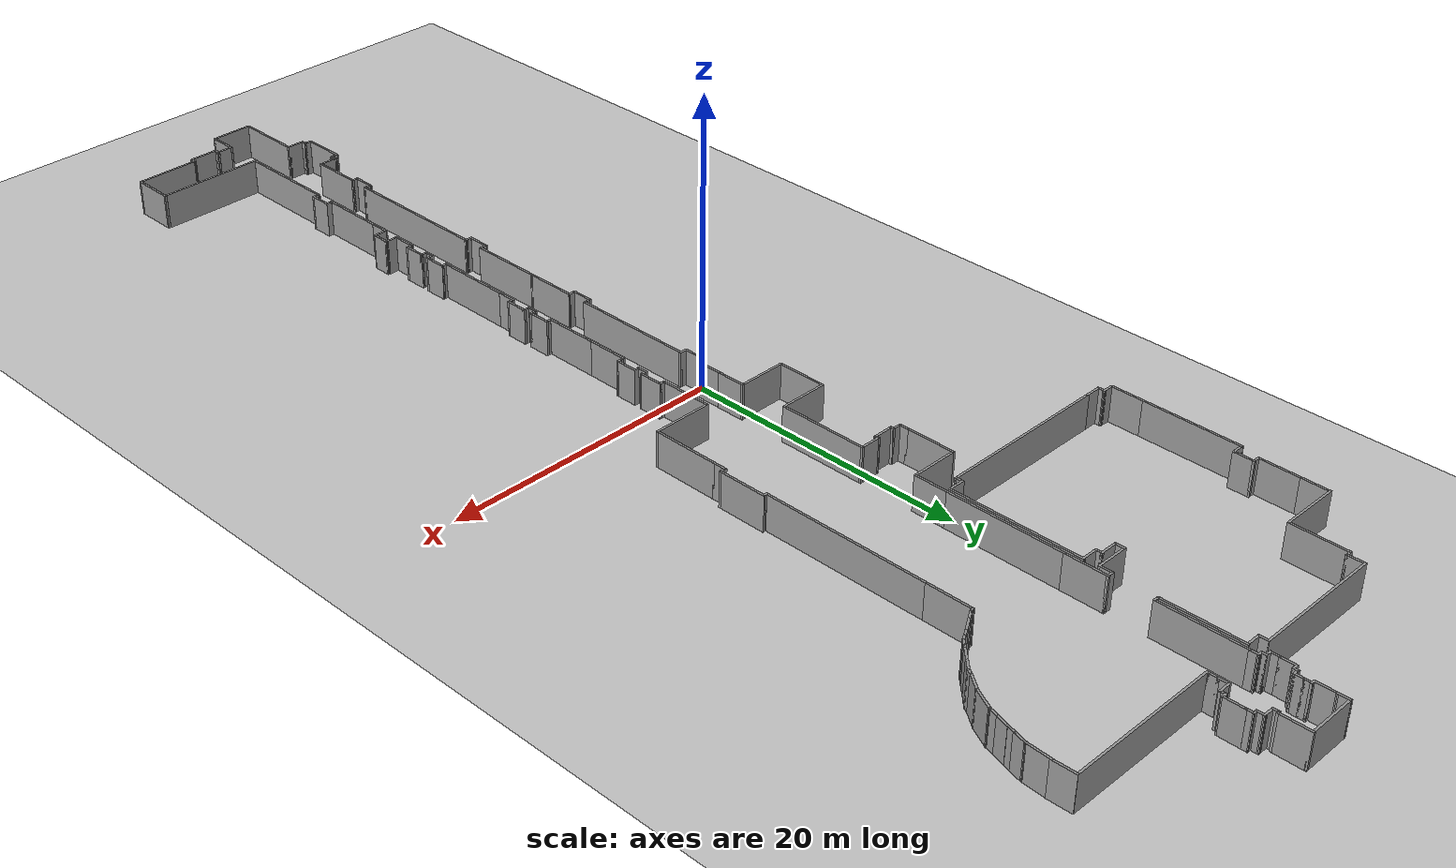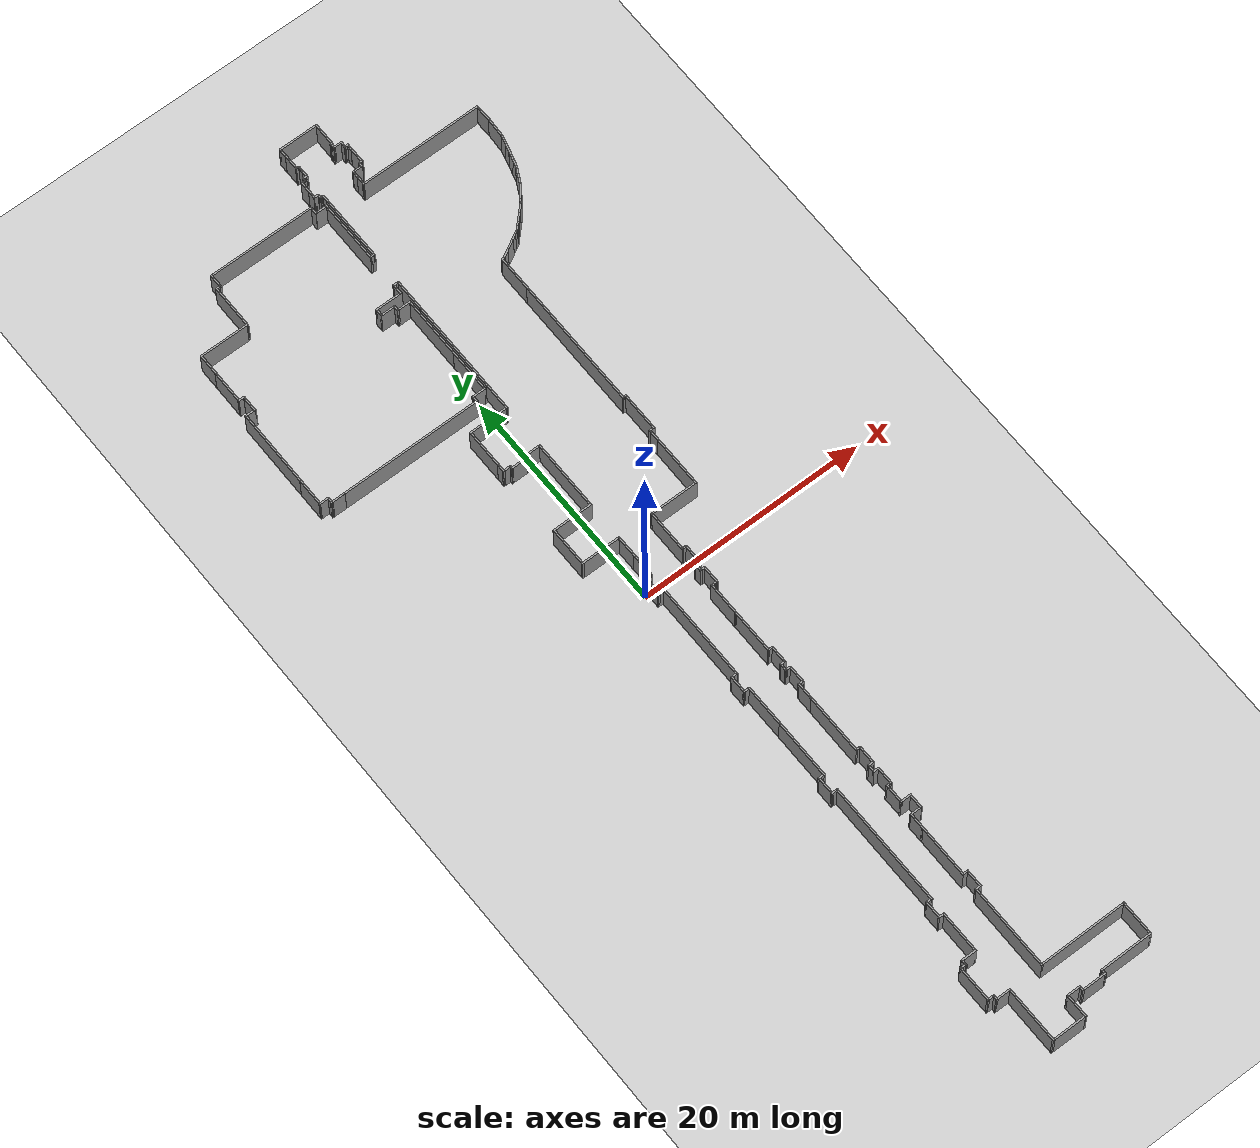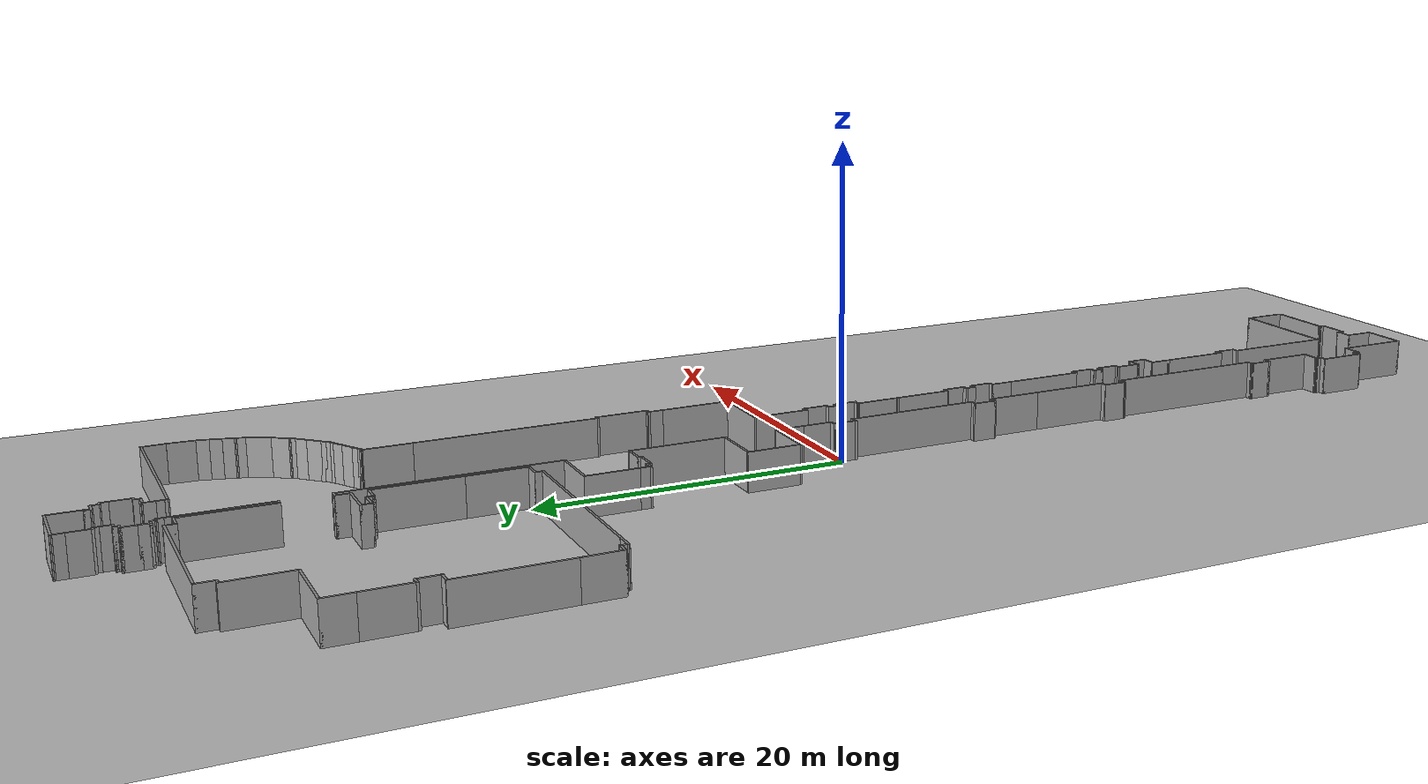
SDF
<sdf version="1.6">
 <world name="default">
  <light name="sun" type="directional">
   <pose>0 0 10 0 -0 0</pose>
   <diffuse>0.8 0.8 0.8 1</diffuse>
   <specular>0.1 0.1 0.1 1</specular>
   <attenuation>
    <range>1000</range>
    <constant>0.9</constant>
    <linear>0.01</linear>
    <quadratic>0.001</quadratic>
   </attenuation>
   <direction>-0.5 0.5 -1</direction>
  </light>
  <model name="ground_plane">
   <static>1</static>
   <link name="link">
    <collision name="collision">
     <geometry><plane><normal>0 0 1</normal><size>100 100</size></plane></geometry>
     <surface><friction><ode><mu>100</mu><mu2>50</mu2></ode></friction></surface>
    </collision>
    <visual name="visual">
     <cast_shadows>0</cast_shadows>
     <geometry><plane><normal>0 0 1</normal><size>100 100</size></plane></geometry>
     <material>
      <script><uri>file://media/materials/scripts/gazebo.material</uri><name>Gazebo/Grey</name></script>
     </material>
    </visual>
   </link>
  </model>
  <gravity>0 0 -9.8</gravity>
  <magnetic_field>6e-06 2.3e-05 -4.2e-05</magnetic_field>
  <atmosphere type="adiabatic"/>
  <physics name="default_physics" default="0" type="ode">
   <max_step_size>0.001</max_step_size>
   <real_time_factor>1</real_time_factor>
   <real_time_update_rate>1000</real_time_update_rate>
  </physics>
  <scene><ambient>0.4 0.4 0.4 1</ambient><background>0.7 0.7 0.7 1</background><shadows>1</shadows></scene>
  <spherical_coordinates>
   <surface_model>EARTH_WGS84</surface_model>
   <latitude_deg>0</latitude_deg>
   <longitude_deg>0</longitude_deg>
   <elevation>0</elevation>
   <heading_deg>0</heading_deg>
  </spherical_coordinates>
  <model name="volen.world">
   <pose>-0.11623 -0.129362 0 0 -0 0</pose>
   <link name="Wall_100">
    <collision name="Wall_100_Collision">
     <geometry><box><size>1.35577 0.15 2.5</size></box></geometry>
     <pose>0 0 1.25 0 -0 0</pose>
    </collision>
    <visual name="Wall_100_Visual">
     <pose>0 0 1.25 0 -0 0</pose>
     <geometry><box><size>1.35577 0.15 2.5</size></box></geometry>
     <material>
      <script><uri>file://media/materials/scripts/gazebo.material</uri><name>Gazebo/Grey</name></script>
      <ambient>1 1 1 1</ambient>
     </material>
    </visual>
    <pose>12.7994 31.5829 0 0 0 -2.21664</pose>
   </link>
   <link name="Wall_101">
    <collision name="Wall_101_Collision">
     <geometry><box><size>0.5 0.15 2.5</size></box></geometry>
     <pose>0 0 1.25 0 -0 0</pose>
    </collision>
    <visual name="Wall_101_Visual">
     <pose>0 0 1.25 0 -0 0</pose>
     <geometry><box><size>0.5 0.15 2.5</size></box></geometry>
     <material>
      <script><uri>file://media/materials/scripts/gazebo.material</uri><name>Gazebo/Grey</name></script>
      <ambient>1 1 1 1</ambient>
     </material>
    </visual>
    <pose>12.349 30.9499 0 0 0 -2.0944</pose>
   </link>
   <link name="Wall_102">
    <collision name="Wall_102_Collision">
     <geometry><box><size>1 0.15 2.5</size></box></geometry>
     <pose>0 0 1.25 0 -0 0</pose>
    </collision>
    <visual name="Wall_102_Visual">
     <pose>0 0 1.25 0 -0 0</pose>
     <geometry><box><size>1 0.15 2.5</size></box></geometry>
     <material>
      <script><uri>file://media/materials/scripts/gazebo.material</uri><name>Gazebo/Grey</name></script>
      <ambient>1 1 1 1</ambient>
     </material>
    </visual>
    <pose>11.961 30.4978 0 0 0 -2.35619</pose>
   </link>
   <link name="Wall_103">
    <collision name="Wall_103_Collision">
     <geometry><box><size>1 0.15 2.5</size></box></geometry>
     <pose>0 0 1.25 0 -0 0</pose>
    </collision>
    <visual name="Wall_103_Visual">
     <pose>0 0 1.25 0 -0 0</pose>
     <geometry><box><size>1 0.15 2.5</size></box></geometry>
     <material>
      <script><uri>file://media/materials/scripts/gazebo.material</uri><name>Gazebo/Grey</name></script>
      <ambient>1 1 1 1</ambient>
     </material>
    </visual>
    <pose>11.36 29.8968 0 0 0 -2.35619</pose>
   </link>
   <link name="Wall_104">
    <collision name="Wall_104_Collision">
     <geometry><box><size>0.5 0.15 2.5</size></box></geometry>
     <pose>0 0 1.25 0 -0 0</pose>
    </collision>
    <visual name="Wall_104_Visual">
     <pose>0 0 1.25 0 -0 0</pose>
     <geometry><box><size>0.5 0.15 2.5</size></box></geometry>
     <material>
      <script><uri>file://media/materials/scripts/gazebo.material</uri><name>Gazebo/Grey</name></script>
      <ambient>1 1 1 1</ambient>
     </material>
    </visual>
    <pose>10.9357 29.4725 0 0 0 -2.35619</pose>
   </link>
   <link name="Wall_105">
    <collision name="Wall_105_Collision">
     <geometry><box><size>0.5 0.15 2.5</size></box></geometry>
     <pose>0 0 1.25 0 -0 0</pose>
    </collision>
    <visual name="Wall_105_Visual">
     <pose>0 0 1.25 0 -0 0</pose>
     <geometry><box><size>0.5 0.15 2.5</size></box></geometry>
     <material>
      <script><uri>file://media/materials/scripts/gazebo.material</uri><name>Gazebo/Grey</name></script>
      <ambient>1 1 1 1</ambient>
     </material>
    </visual>
    <pose>10.6882 29.225 0 0 0 -2.35619</pose>
   </link>
   <link name="Wall_106">
    <collision name="Wall_106_Collision">
     <geometry><box><size>0.5 0.15 2.5</size></box></geometry>
     <pose>0 0 1.25 0 -0 0</pose>
    </collision>
    <visual name="Wall_106_Visual">
     <pose>0 0 1.25 0 -0 0</pose>
     <geometry><box><size>0.5 0.15 2.5</size></box></geometry>
     <material>
      <script><uri>file://media/materials/scripts/gazebo.material</uri><name>Gazebo/Grey</name></script>
      <ambient>1 1 1 1</ambient>
     </material>
    </visual>
    <pose>10.4129 29.0138 0 0 0 -2.61799</pose>
   </link>
   <link name="Wall_108">
    <collision name="Wall_108_Collision">
     <geometry><box><size>0.75 0.15 2.5</size></box></geometry>
     <pose>0 0 1.25 0 -0 0</pose>
    </collision>
    <visual name="Wall_108_Visual">
     <pose>0 0 1.25 0 -0 0</pose>
     <geometry><box><size>0.75 0.15 2.5</size></box></geometry>
     <material>
      <script><uri>file://media/materials/scripts/gazebo.material</uri><name>Gazebo/Grey</name></script>
      <ambient>1 1 1 1</ambient>
     </material>
    </visual>
    <pose>10.0015 28.7763 0 0 0 -2.61799</pose>
   </link>
   <link name="Wall_109">
    <collision name="Wall_109_Collision">
     <geometry><box><size>1 0.15 2.5</size></box></geometry>
     <pose>0 0 1.25 0 -0 0</pose>
    </collision>
    <visual name="Wall_109_Visual">
     <pose>0 0 1.25 0 -0 0</pose>
     <geometry><box><size>1 0.15 2.5</size></box></geometry>
     <material>
      <script><uri>file://media/materials/scripts/gazebo.material</uri><name>Gazebo/Grey</name></script>
      <ambient>1 1 1 1</ambient>
     </material>
    </visual>
    <pose>9.37367 28.4138 0 0 0 -2.61799</pose>
   </link>
   <link name="Wall_110">
    <collision name="Wall_110_Collision">
     <geometry><box><size>0.75 0.15 2.5</size></box></geometry>
     <pose>0 0 1.25 0 -0 0</pose>
    </collision>
    <visual name="Wall_110_Visual">
     <pose>0 0 1.25 0 -0 0</pose>
     <geometry><box><size>0.75 0.15 2.5</size></box></geometry>
     <material>
      <script><uri>file://media/materials/scripts/gazebo.material</uri><name>Gazebo/Grey</name></script>
      <ambient>1 1 1 1</ambient>
     </material>
    </visual>
    <pose>8.7458 28.0513 0 0 0 -2.61799</pose>
   </link>
   <link name="Wall_111">
    <collision name="Wall_111_Collision">
     <geometry><box><size>0.25 0.15 2.5</size></box></geometry>
     <pose>0 0 1.25 0 -0 0</pose>
    </collision>
    <visual name="Wall_111_Visual">
     <pose>0 0 1.25 0 -0 0</pose>
     <geometry><box><size>0.25 0.15 2.5</size></box></geometry>
     <material>
      <script><uri>file://media/materials/scripts/gazebo.material</uri><name>Gazebo/Grey</name></script>
      <ambient>1 1 1 1</ambient>
     </material>
    </visual>
    <pose>8.44269 27.8763 0 0 0 -2.61799</pose>
   </link>
   <link name="Wall_112">
    <collision name="Wall_112_Collision">
     <geometry><box><size>0.25 0.15 2.5</size></box></geometry>
     <pose>0 0 1.25 0 -0 0</pose>
    </collision>
    <visual name="Wall_112_Visual">
     <pose>0 0 1.25 0 -0 0</pose>
     <geometry><box><size>0.25 0.15 2.5</size></box></geometry>
     <material>
      <script><uri>file://media/materials/scripts/gazebo.material</uri><name>Gazebo/Grey</name></script>
      <ambient>1 1 1 1</ambient>
     </material>
    </visual>
    <pose>8.3511 27.8383 0 0 0 -2.87979</pose>
   </link>
   <link name="Wall_113">
    <collision name="Wall_113_Collision">
     <geometry><box><size>0.25 0.15 2.5</size></box></geometry>
     <pose>0 0 1.25 0 -0 0</pose>
    </collision>
    <visual name="Wall_113_Visual">
     <pose>0 0 1.25 0 -0 0</pose>
     <geometry><box><size>0.25 0.15 2.5</size></box></geometry>
     <material>
      <script><uri>file://media/materials/scripts/gazebo.material</uri><name>Gazebo/Grey</name></script>
      <ambient>1 1 1 1</ambient>
     </material>
    </visual>
    <pose>8.2545 27.8124 0 0 0 -2.87979</pose>
   </link>
   <link name="Wall_114">
    <collision name="Wall_114_Collision">
     <geometry><box><size>3.25 0.15 2.5</size></box></geometry>
     <pose>0 0 1.25 0 -0 0</pose>
    </collision>
    <visual name="Wall_114_Visual">
     <pose>0 0 1.25 0 -0 0</pose>
     <geometry><box><size>3.25 0.15 2.5</size></box></geometry>
     <material>
      <script><uri>file://media/materials/scripts/gazebo.material</uri><name>Gazebo/Grey</name></script>
      <ambient>1 1 1 1</ambient>
     </material>
    </visual>
    <pose>8.20621 26.2495 0 0 0 -1.5708</pose>
   </link>
   <link name="Wall_116">
    <collision name="Wall_116_Collision">
     <geometry><box><size>11.75 0.15 2.5</size></box></geometry>
     <pose>0 0 1.25 0 -0 0</pose>
    </collision>
    <visual name="Wall_116_Visual">
     <pose>0 0 1.25 0 -0 0</pose>
     <geometry><box><size>11.75 0.15 2.5</size></box></geometry>
     <material>
      <script><uri>file://media/materials/scripts/gazebo.material</uri><name>Gazebo/Grey</name></script>
      <ambient>1 1 1 1</ambient>
     </material>
    </visual>
    <pose>8.20622 18.8994 0 0 0 -1.57079</pose>
   </link>
   <link name="Wall_118">
    <collision name="Wall_118_Collision">
     <geometry><box><size>0.38 0.15 2.5</size></box></geometry>
     <pose>0 0 1.25 0 -0 0</pose>
    </collision>
    <visual name="Wall_118_Visual">
     <pose>0 0 1.25 0 -0 0</pose>
     <geometry><box><size>0.38 0.15 2.5</size></box></geometry>
     <material>
      <script><uri>file://media/materials/scripts/gazebo.material</uri><name>Gazebo/Grey</name></script>
      <ambient>1 1 1 1</ambient>
     </material>
    </visual>
    <pose>8.32123 13.0994 0 0 -0 0</pose>
   </link>
   <link name="Wall_121">
    <collision name="Wall_121_Collision">
     <geometry><box><size>3.5 0.15 2.5</size></box></geometry>
     <pose>0 0 1.25 0 -0 0</pose>
    </collision>
    <visual name="Wall_121_Visual">
     <pose>0 0 1.25 0 -0 0</pose>
     <geometry><box><size>3.5 0.15 2.5</size></box></geometry>
     <material>
      <script><uri>file://media/materials/scripts/gazebo.material</uri><name>Gazebo/Grey</name></script>
      <ambient>1 1 1 1</ambient>
     </material>
    </visual>
    <pose>8.43623 11.4244 0 0 0 -1.5708</pose>
   </link>
   <link name="Wall_122">
    <collision name="Wall_122_Collision">
     <geometry><box><size>0.5 0.15 2.5</size></box></geometry>
     <pose>0 0 1.25 0 -0 0</pose>
    </collision>
    <visual name="Wall_122_Visual">
     <pose>0 0 1.25 0 -0 0</pose>
     <geometry><box><size>0.5 0.15 2.5</size></box></geometry>
     <material>
      <script><uri>file://media/materials/scripts/gazebo.material</uri><name>Gazebo/Grey</name></script>
      <ambient>1 1 1 1</ambient>
     </material>
    </visual>
    <pose>8.26123 9.74936 0 0 -0 3.14159</pose>
   </link>
   <link name="Wall_123">
    <collision name="Wall_123_Collision">
     <geometry><box><size>1 0.15 2.5</size></box></geometry>
     <pose>0 0 1.25 0 -0 0</pose>
    </collision>
    <visual name="Wall_123_Visual">
     <pose>0 0 1.25 0 -0 0</pose>
     <geometry><box><size>1 0.15 2.5</size></box></geometry>
     <material>
      <script><uri>file://media/materials/scripts/gazebo.material</uri><name>Gazebo/Grey</name></script>
      <ambient>1 1 1 1</ambient>
     </material>
    </visual>
    <pose>8.08623 9.32436 0 0 0 -1.5708</pose>
   </link>
   <link name="Wall_125">
    <collision name="Wall_125_Collision">
     <geometry><box><size>4.75 0.15 2.5</size></box></geometry>
     <pose>0 0 1.25 0 -0 0</pose>
    </collision>
    <visual name="Wall_125_Visual">
     <pose>0 0 1.25 0 -0 0</pose>
     <geometry><box><size>4.75 0.15 2.5</size></box></geometry>
     <material>
      <script><uri>file://media/materials/scripts/gazebo.material</uri><name>Gazebo/Grey</name></script>
      <ambient>1 1 1 1</ambient>
     </material>
    </visual>
    <pose>8.08623 6.59936 0 0 0 -1.5708</pose>
   </link>
   <link name="Wall_126">
    <collision name="Wall_126_Collision">
     <geometry><box><size>4.25 0.15 2.5</size></box></geometry>
     <pose>0 0 1.25 0 -0 0</pose>
    </collision>
    <visual name="Wall_126_Visual">
     <pose>0 0 1.25 0 -0 0</pose>
     <geometry><box><size>4.25 0.15 2.5</size></box></geometry>
     <material>
      <script><uri>file://media/materials/scripts/gazebo.material</uri><name>Gazebo/Grey</name></script>
      <ambient>1 1 1 1</ambient>
     </material>
    </visual>
    <pose>6.03623 4.29936 0 0 -0 3.14159</pose>
   </link>
   <link name="Wall_128">
    <collision name="Wall_128_Collision">
     <geometry><box><size>3.75 0.15 2.5</size></box></geometry>
     <pose>0 0 1.25 0 -0 0</pose>
    </collision>
    <visual name="Wall_128_Visual">
     <pose>0 0 1.25 0 -0 0</pose>
     <geometry><box><size>3.75 0.15 2.5</size></box></geometry>
     <material>
      <script><uri>file://media/materials/scripts/gazebo.material</uri><name>Gazebo/Grey</name></script>
      <ambient>1 1 1 1</ambient>
     </material>
    </visual>
    <pose>3.98623 2.49936 0 0 0 -1.5708</pose>
   </link>
   <link name="Wall_129">
    <collision name="Wall_129_Collision">
     <geometry><box><size>0.5 0.15 2.5</size></box></geometry>
     <pose>0 0 1.25 0 -0 0</pose>
    </collision>
    <visual name="Wall_129_Visual">
     <pose>0 0 1.25 0 -0 0</pose>
     <geometry><box><size>0.5 0.15 2.5</size></box></geometry>
     <material>
      <script><uri>file://media/materials/scripts/gazebo.material</uri><name>Gazebo/Grey</name></script>
      <ambient>1 1 1 1</ambient>
     </material>
    </visual>
    <pose>4.16123 0.699362 0 0 -0 0</pose>
   </link>
   <link name="Wall_130">
    <collision name="Wall_130_Collision">
     <geometry><box><size>1.75 0.15 2.5</size></box></geometry>
     <pose>0 0 1.25 0 -0 0</pose>
    </collision>
    <visual name="Wall_130_Visual">
     <pose>0 0 1.25 0 -0 0</pose>
     <geometry><box><size>1.75 0.15 2.5</size></box></geometry>
     <material>
      <script><uri>file://media/materials/scripts/gazebo.material</uri><name>Gazebo/Grey</name></script>
      <ambient>1 1 1 1</ambient>
     </material>
    </visual>
    <pose>4.33623 -0.100638 0 0 0 -1.5708</pose>
   </link>
   <link name="Wall_131">
    <collision name="Wall_131_Collision">
     <geometry><box><size>0.5 0.15 2.5</size></box></geometry>
     <pose>0 0 1.25 0 -0 0</pose>
    </collision>
    <visual name="Wall_131_Visual">
     <pose>0 0 1.25 0 -0 0</pose>
     <geometry><box><size>0.5 0.15 2.5</size></box></geometry>
     <material>
      <script><uri>file://media/materials/scripts/gazebo.material</uri><name>Gazebo/Grey</name></script>
      <ambient>1 1 1 1</ambient>
     </material>
    </visual>
    <pose>4.16123 -0.900638 0 0 -0 3.14159</pose>
   </link>
   <link name="Wall_132">
    <collision name="Wall_132_Collision">
     <geometry><box><size>0.75 0.15 2.5</size></box></geometry>
     <pose>0 0 1.25 0 -0 0</pose>
    </collision>
    <visual name="Wall_132_Visual">
     <pose>0 0 1.25 0 -0 0</pose>
     <geometry><box><size>0.75 0.15 2.5</size></box></geometry>
     <material>
      <script><uri>file://media/materials/scripts/gazebo.material</uri><name>Gazebo/Grey</name></script>
      <ambient>1 1 1 1</ambient>
     </material>
    </visual>
    <pose>3.98623 -1.20064 0 0 0 -1.5708</pose>
   </link>
   <link name="Wall_133">
    <collision name="Wall_133_Collision">
     <geometry><box><size>0.5 0.15 2.5</size></box></geometry>
     <pose>0 0 1.25 0 -0 0</pose>
    </collision>
    <visual name="Wall_133_Visual">
     <pose>0 0 1.25 0 -0 0</pose>
     <geometry><box><size>0.5 0.15 2.5</size></box></geometry>
     <material>
      <script><uri>file://media/materials/scripts/gazebo.material</uri><name>Gazebo/Grey</name></script>
      <ambient>1 1 1 1</ambient>
     </material>
    </visual>
    <pose>4.16123 -1.50064 0 0 -0 0</pose>
   </link>
   <link name="Wall_135">
    <collision name="Wall_135_Collision">
     <geometry><box><size>1.6 0.15 2.5</size></box></geometry>
     <pose>0 0 1.25 0 -0 0</pose>
    </collision>
    <visual name="Wall_135_Visual">
     <pose>0 0 1.25 0 -0 0</pose>
     <geometry><box><size>1.6 0.15 2.5</size></box></geometry>
     <material>
      <script><uri>file://media/materials/scripts/gazebo.material</uri><name>Gazebo/Grey</name></script>
      <ambient>1 1 1 1</ambient>
     </material>
    </visual>
    <pose>4.33623 -2.22564 0 0 0 -1.5708</pose>
   </link>
   <link name="Wall_136">
    <collision name="Wall_136_Collision">
     <geometry><box><size>0.480681 0.15 2.5</size></box></geometry>
     <pose>0 0 1.25 0 -0 0</pose>
    </collision>
    <visual name="Wall_136_Visual">
     <pose>0 0 1.25 0 -0 0</pose>
     <geometry><box><size>0.480681 0.15 2.5</size></box></geometry>
     <material>
      <script><uri>file://media/materials/scripts/gazebo.material</uri><name>Gazebo/Grey</name></script>
      <ambient>1 1 1 1</ambient>
     </material>
    </visual>
    <pose>4.17098 -2.94965 0 0 -0 3.13564</pose>
   </link>
   <link name="Wall_137">
    <collision name="Wall_137_Collision">
     <geometry><box><size>0.280454 0.15 2.5</size></box></geometry>
     <pose>0 0 1.25 0 -0 0</pose>
    </collision>
    <visual name="Wall_137_Visual">
     <pose>0 0 1.25 0 -0 0</pose>
     <geometry><box><size>0.280454 0.15 2.5</size></box></geometry>
     <material>
      <script><uri>file://media/materials/scripts/gazebo.material</uri><name>Gazebo/Grey</name></script>
      <ambient>1 1 1 1</ambient>
     </material>
    </visual>
    <pose>3.94053 -2.94916 0 0 -0 3.04965</pose>
   </link>
   <link name="Wall_138">
    <collision name="Wall_138_Collision">
     <geometry><box><size>3 0.15 2.5</size></box></geometry>
     <pose>0 0 1.25 0 -0 0</pose>
    </collision>
    <visual name="Wall_138_Visual">
     <pose>0 0 1.25 0 -0 0</pose>
     <geometry><box><size>3 0.15 2.5</size></box></geometry>
     <material>
      <script><uri>file://media/materials/scripts/gazebo.material</uri><name>Gazebo/Grey</name></script>
      <ambient>1 1 1 1</ambient>
     </material>
    </visual>
    <pose>3.87532 -4.37675 0 0 0 -1.5708</pose>
   </link>
   <link name="Wall_140">
    <collision name="Wall_140_Collision">
     <geometry><box><size>3.90751 0.15 2.5</size></box></geometry>
     <pose>0 0 1.25 0 -0 0</pose>
    </collision>
    <visual name="Wall_140_Visual">
     <pose>0 0 1.25 0 -0 0</pose>
     <geometry><box><size>3.90751 0.15 2.5</size></box></geometry>
     <material>
      <script><uri>file://media/materials/scripts/gazebo.material</uri><name>Gazebo/Grey</name></script>
      <ambient>1 1 1 1</ambient>
     </material>
    </visual>
    <pose>3.88078 -7.67189 0 0 0 -1.56789</pose>
   </link>
   <link name="Wall_141">
    <collision name="Wall_141_Collision">
     <geometry><box><size>0.5 0.15 2.5</size></box></geometry>
     <pose>0 0 1.25 0 -0 0</pose>
    </collision>
    <visual name="Wall_141_Visual">
     <pose>0 0 1.25 0 -0 0</pose>
     <geometry><box><size>0.5 0.15 2.5</size></box></geometry>
     <material>
      <script><uri>file://media/materials/scripts/gazebo.material</uri><name>Gazebo/Grey</name></script>
      <ambient>1 1 1 1</ambient>
     </material>
    </visual>
    <pose>4.06123 -9.55064 0 0 -0 0</pose>
   </link>
   <link name="Wall_142">
    <collision name="Wall_142_Collision">
     <geometry><box><size>1.6 0.15 2.5</size></box></geometry>
     <pose>0 0 1.25 0 -0 0</pose>
    </collision>
    <visual name="Wall_142_Visual">
     <pose>0 0 1.25 0 -0 0</pose>
     <geometry><box><size>1.6 0.15 2.5</size></box></geometry>
     <material>
      <script><uri>file://media/materials/scripts/gazebo.material</uri><name>Gazebo/Grey</name></script>
      <ambient>1 1 1 1</ambient>
     </material>
    </visual>
    <pose>4.23623 -10.2756 0 0 0 -1.5708</pose>
   </link>
   <link name="Wall_145">
    <collision name="Wall_145_Collision">
     <geometry><box><size>0.5 0.15 2.5</size></box></geometry>
     <pose>0 0 1.25 0 -0 0</pose>
    </collision>
    <visual name="Wall_145_Visual">
     <pose>0 0 1.25 0 -0 0</pose>
     <geometry><box><size>0.5 0.15 2.5</size></box></geometry>
     <material>
      <script><uri>file://media/materials/scripts/gazebo.material</uri><name>Gazebo/Grey</name></script>
      <ambient>1 1 1 1</ambient>
     </material>
    </visual>
    <pose>4.06123 -11.0006 0 0 -0 3.14159</pose>
   </link>
   <link name="Wall_146">
    <collision name="Wall_146_Collision">
     <geometry><box><size>0.75 0.15 2.5</size></box></geometry>
     <pose>0 0 1.25 0 -0 0</pose>
    </collision>
    <visual name="Wall_146_Visual">
     <pose>0 0 1.25 0 -0 0</pose>
     <geometry><box><size>0.75 0.15 2.5</size></box></geometry>
     <material>
      <script><uri>file://media/materials/scripts/gazebo.material</uri><name>Gazebo/Grey</name></script>
      <ambient>1 1 1 1</ambient>
     </material>
    </visual>
    <pose>3.88623 -11.3006 0 0 0 -1.5708</pose>
   </link>
   <link name="Wall_147">
    <collision name="Wall_147_Collision">
     <geometry><box><size>0.55 0.15 2.5</size></box></geometry>
     <pose>0 0 1.25 0 -0 0</pose>
    </collision>
    <visual name="Wall_147_Visual">
     <pose>0 0 1.25 0 -0 0</pose>
     <geometry><box><size>0.55 0.15 2.5</size></box></geometry>
     <material>
      <script><uri>file://media/materials/scripts/gazebo.material</uri><name>Gazebo/Grey</name></script>
      <ambient>1 1 1 1</ambient>
     </material>
    </visual>
    <pose>4.08623 -11.6006 0 0 -0 0</pose>
   </link>
   <link name="Wall_149">
    <collision name="Wall_149_Collision">
     <geometry><box><size>1.6 0.15 2.5</size></box></geometry>
     <pose>0 0 1.25 0 -0 0</pose>
    </collision>
    <visual name="Wall_149_Visual">
     <pose>0 0 1.25 0 -0 0</pose>
     <geometry><box><size>1.6 0.15 2.5</size></box></geometry>
     <material>
      <script><uri>file://media/materials/scripts/gazebo.material</uri><name>Gazebo/Grey</name></script>
      <ambient>1 1 1 1</ambient>
     </material>
    </visual>
    <pose>4.28623 -12.3256 0 0 0 -1.5708</pose>
   </link>
   <link name="Wall_151">
    <collision name="Wall_151_Collision">
     <geometry><box><size>0.5 0.15 2.5</size></box></geometry>
     <pose>0 0 1.25 0 -0 0</pose>
    </collision>
    <visual name="Wall_151_Visual">
     <pose>0 0 1.25 0 -0 0</pose>
     <geometry><box><size>0.5 0.15 2.5</size></box></geometry>
     <material>
      <script><uri>file://media/materials/scripts/gazebo.material</uri><name>Gazebo/Grey</name></script>
      <ambient>1 1 1 1</ambient>
     </material>
    </visual>
    <pose>4.11123 -13.0506 0 0 -0 3.14159</pose>
   </link>
   <link name="Wall_152">
    <collision name="Wall_152_Collision">
     <geometry><box><size>1.5 0.15 2.5</size></box></geometry>
     <pose>0 0 1.25 0 -0 0</pose>
    </collision>
    <visual name="Wall_152_Visual">
     <pose>0 0 1.25 0 -0 0</pose>
     <geometry><box><size>1.5 0.15 2.5</size></box></geometry>
     <material>
      <script><uri>file://media/materials/scripts/gazebo.material</uri><name>Gazebo/Grey</name></script>
      <ambient>1 1 1 1</ambient>
     </material>
    </visual>
    <pose>3.93623 -13.7256 0 0 0 -1.5708</pose>
   </link>
   <link name="Wall_154">
    <collision name="Wall_154_Collision">
     <geometry><box><size>5.4 0.15 2.5</size></box></geometry>
     <pose>0 0 1.25 0 -0 0</pose>
    </collision>
    <visual name="Wall_154_Visual">
     <pose>0 0 1.25 0 -0 0</pose>
     <geometry><box><size>5.4 0.15 2.5</size></box></geometry>
     <material>
      <script><uri>file://media/materials/scripts/gazebo.material</uri><name>Gazebo/Grey</name></script>
      <ambient>1 1 1 1</ambient>
     </material>
    </visual>
    <pose>3.93623 -17.0256 0 0 0 -1.5708</pose>
   </link>
   <link name="Wall_156">
    <collision name="Wall_156_Collision">
     <geometry><box><size>0.5 0.15 2.5</size></box></geometry>
     <pose>0 0 1.25 0 -0 0</pose>
    </collision>
    <visual name="Wall_156_Visual">
     <pose>0 0 1.25 0 -0 0</pose>
     <geometry><box><size>0.5 0.15 2.5</size></box></geometry>
     <material>
      <script><uri>file://media/materials/scripts/gazebo.material</uri><name>Gazebo/Grey</name></script>
      <ambient>1 1 1 1</ambient>
     </material>
    </visual>
    <pose>4.11123 -19.6506 0 0 -0 0</pose>
   </link>
   <link name="Wall_157">
    <collision name="Wall_157_Collision">
     <geometry><box><size>1.65 0.15 2.5</size></box></geometry>
     <pose>0 0 1.25 0 -0 0</pose>
    </collision>
    <visual name="Wall_157_Visual">
     <pose>0 0 1.25 0 -0 0</pose>
     <geometry><box><size>1.65 0.15 2.5</size></box></geometry>
     <material>
      <script><uri>file://media/materials/scripts/gazebo.material</uri><name>Gazebo/Grey</name></script>
      <ambient>1 1 1 1</ambient>
     </material>
    </visual>
    <pose>4.28623 -20.4006 0 0 0 -1.5708</pose>
   </link>
   <link name="Wall_159">
    <collision name="Wall_159_Collision">
     <geometry><box><size>0.55 0.15 2.5</size></box></geometry>
     <pose>0 0 1.25 0 -0 0</pose>
    </collision>
    <visual name="Wall_159_Visual">
     <pose>0 0 1.25 0 -0 0</pose>
     <geometry><box><size>0.55 0.15 2.5</size></box></geometry>
     <material>
      <script><uri>file://media/materials/scripts/gazebo.material</uri><name>Gazebo/Grey</name></script>
      <ambient>1 1 1 1</ambient>
     </material>
    </visual>
    <pose>4.08623 -21.1506 0 0 -0 3.14159</pose>
   </link>
   <link name="Wall_161">
    <collision name="Wall_161_Collision">
     <geometry><box><size>0.75 0.15 2.5</size></box></geometry>
     <pose>0 0 1.25 0 -0 0</pose>
    </collision>
    <visual name="Wall_161_Visual">
     <pose>0 0 1.25 0 -0 0</pose>
     <geometry><box><size>0.75 0.15 2.5</size></box></geometry>
     <material>
      <script><uri>file://media/materials/scripts/gazebo.material</uri><name>Gazebo/Grey</name></script>
      <ambient>1 1 1 1</ambient>
     </material>
    </visual>
    <pose>3.88623 -21.4506 0 0 0 -1.5708</pose>
   </link>
   <link name="Wall_162">
    <collision name="Wall_162_Collision">
     <geometry><box><size>0.55 0.15 2.5</size></box></geometry>
     <pose>0 0 1.25 0 -0 0</pose>
    </collision>
    <visual name="Wall_162_Visual">
     <pose>0 0 1.25 0 -0 0</pose>
     <geometry><box><size>0.55 0.15 2.5</size></box></geometry>
     <material>
      <script><uri>file://media/materials/scripts/gazebo.material</uri><name>Gazebo/Grey</name></script>
      <ambient>1 1 1 1</ambient>
     </material>
    </visual>
    <pose>4.08623 -21.7506 0 0 -0 0</pose>
   </link>
   <link name="Wall_166">
    <collision name="Wall_166_Collision">
     <geometry><box><size>1.6 0.15 2.5</size></box></geometry>
     <pose>0 0 1.25 0 -0 0</pose>
    </collision>
    <visual name="Wall_166_Visual">
     <pose>0 0 1.25 0 -0 0</pose>
     <geometry><box><size>1.6 0.15 2.5</size></box></geometry>
     <material>
      <script><uri>file://media/materials/scripts/gazebo.material</uri><name>Gazebo/Grey</name></script>
      <ambient>1 1 1 1</ambient>
     </material>
    </visual>
    <pose>4.28623 -22.4756 0 0 0 -1.5708</pose>
   </link>
   <link name="Wall_168">
    <collision name="Wall_168_Collision">
     <geometry><box><size>0.5 0.15 2.5</size></box></geometry>
     <pose>0 0 1.25 0 -0 0</pose>
    </collision>
    <visual name="Wall_168_Visual">
     <pose>0 0 1.25 0 -0 0</pose>
     <geometry><box><size>0.5 0.15 2.5</size></box></geometry>
     <material>
      <script><uri>file://media/materials/scripts/gazebo.material</uri><name>Gazebo/Grey</name></script>
      <ambient>1 1 1 1</ambient>
     </material>
    </visual>
    <pose>4.11123 -23.2006 0 0 -0 3.14159</pose>
   </link>
   <link name="Wall_169">
    <collision name="Wall_169_Collision">
     <geometry><box><size>1.75 0.15 2.5</size></box></geometry>
     <pose>0 0 1.25 0 -0 0</pose>
    </collision>
    <visual name="Wall_169_Visual">
     <pose>0 0 1.25 0 -0 0</pose>
     <geometry><box><size>1.75 0.15 2.5</size></box></geometry>
     <material>
      <script><uri>file://media/materials/scripts/gazebo.material</uri><name>Gazebo/Grey</name></script>
      <ambient>1 1 1 1</ambient>
     </material>
    </visual>
    <pose>3.93623 -24.0006 0 0 0 -1.5708</pose>
   </link>
   <link name="Wall_170">
    <collision name="Wall_170_Collision">
     <geometry><box><size>1 0.15 2.5</size></box></geometry>
     <pose>0 0 1.25 0 -0 0</pose>
    </collision>
    <visual name="Wall_170_Visual">
     <pose>0 0 1.25 0 -0 0</pose>
     <geometry><box><size>1 0.15 2.5</size></box></geometry>
     <material>
      <script><uri>file://media/materials/scripts/gazebo.material</uri><name>Gazebo/Grey</name></script>
      <ambient>1 1 1 1</ambient>
     </material>
    </visual>
    <pose>4.36123 -24.8006 0 0 -0 0</pose>
   </link>
   <link name="Wall_172">
    <collision name="Wall_172_Collision">
     <geometry><box><size>1.35 0.15 2.5</size></box></geometry>
     <pose>0 0 1.25 0 -0 0</pose>
    </collision>
    <visual name="Wall_172_Visual">
     <pose>0 0 1.25 0 -0 0</pose>
     <geometry><box><size>1.35 0.15 2.5</size></box></geometry>
     <material>
      <script><uri>file://media/materials/scripts/gazebo.material</uri><name>Gazebo/Grey</name></script>
      <ambient>1 1 1 1</ambient>
     </material>
    </visual>
    <pose>4.78193 -25.4006 0 0 0 -1.57796</pose>
   </link>
   <link name="Wall_174">
    <collision name="Wall_174_Collision">
     <geometry><box><size>1.05 0.15 2.5</size></box></geometry>
     <pose>0 0 1.25 0 -0 0</pose>
    </collision>
    <visual name="Wall_174_Visual">
     <pose>0 0 1.25 0 -0 0</pose>
     <geometry><box><size>1.05 0.15 2.5</size></box></geometry>
     <material>
      <script><uri>file://media/materials/scripts/gazebo.material</uri><name>Gazebo/Grey</name></script>
      <ambient>1 1 1 1</ambient>
     </material>
    </visual>
    <pose>4.32763 -26.0006 0 0 -0 3.14159</pose>
   </link>
   <link name="Wall_176">
    <collision name="Wall_176_Collision">
     <geometry><box><size>1.5 0.15 2.5</size></box></geometry>
     <pose>0 0 1.25 0 -0 0</pose>
    </collision>
    <visual name="Wall_176_Visual">
     <pose>0 0 1.25 0 -0 0</pose>
     <geometry><box><size>1.5 0.15 2.5</size></box></geometry>
     <material>
      <script><uri>file://media/materials/scripts/gazebo.material</uri><name>Gazebo/Grey</name></script>
      <ambient>1 1 1 1</ambient>
     </material>
    </visual>
    <pose>3.87743 -26.6756 0 0 0 -1.57109</pose>
   </link>
   <link name="Wall_178">
    <collision name="Wall_178_Collision">
     <geometry><box><size>4.7 0.15 2.5</size></box></geometry>
     <pose>0 0 1.25 0 -0 0</pose>
    </collision>
    <visual name="Wall_178_Visual">
     <pose>0 0 1.25 0 -0 0</pose>
     <geometry><box><size>4.7 0.15 2.5</size></box></geometry>
     <material>
      <script><uri>file://media/materials/scripts/gazebo.material</uri><name>Gazebo/Grey</name></script>
      <ambient>1 1 1 1</ambient>
     </material>
    </visual>
    <pose>3.87723 -29.6256 0 0 0 -1.5708</pose>
   </link>
   <link name="Wall_180">
    <collision name="Wall_180_Collision">
     <geometry><box><size>0.55 0.15 2.5</size></box></geometry>
     <pose>0 0 1.25 0 -0 0</pose>
    </collision>
    <visual name="Wall_180_Visual">
     <pose>0 0 1.25 0 -0 0</pose>
     <geometry><box><size>0.55 0.15 2.5</size></box></geometry>
     <material>
      <script><uri>file://media/materials/scripts/gazebo.material</uri><name>Gazebo/Grey</name></script>
      <ambient>1 1 1 1</ambient>
     </material>
    </visual>
    <pose>4.07723 -31.9006 0 0 -0 0</pose>
   </link>
   <link name="Wall_182">
    <collision name="Wall_182_Collision">
     <geometry><box><size>1.6 0.15 2.5</size></box></geometry>
     <pose>0 0 1.25 0 -0 0</pose>
    </collision>
    <visual name="Wall_182_Visual">
     <pose>0 0 1.25 0 -0 0</pose>
     <geometry><box><size>1.6 0.15 2.5</size></box></geometry>
     <material>
      <script><uri>file://media/materials/scripts/gazebo.material</uri><name>Gazebo/Grey</name></script>
      <ambient>1 1 1 1</ambient>
     </material>
    </visual>
    <pose>4.27723 -32.6256 0 0 0 -1.5708</pose>
   </link>
   <link name="Wall_184">
    <collision name="Wall_184_Collision">
     <geometry><box><size>0.55 0.15 2.5</size></box></geometry>
     <pose>0 0 1.25 0 -0 0</pose>
    </collision>
    <visual name="Wall_184_Visual">
     <pose>0 0 1.25 0 -0 0</pose>
     <geometry><box><size>0.55 0.15 2.5</size></box></geometry>
     <material>
      <script><uri>file://media/materials/scripts/gazebo.material</uri><name>Gazebo/Grey</name></script>
      <ambient>1 1 1 1</ambient>
     </material>
    </visual>
    <pose>4.07723 -33.3506 0 0 -0 3.14159</pose>
   </link>
   <link name="Wall_187">
    <collision name="Wall_187_Collision">
     <geometry><box><size>7.5 0.15 2.5</size></box></geometry>
     <pose>0 0 1.25 0 -0 0</pose>
    </collision>
    <visual name="Wall_187_Visual">
     <pose>0 0 1.25 0 -0 0</pose>
     <geometry><box><size>7.5 0.15 2.5</size></box></geometry>
     <material>
      <script><uri>file://media/materials/scripts/gazebo.material</uri><name>Gazebo/Grey</name></script>
      <ambient>1 1 1 1</ambient>
     </material>
    </visual>
    <pose>3.87723 -37.0256 0 0 0 -1.5708</pose>
   </link>
   <link name="Wall_188">
    <collision name="Wall_188_Collision">
     <geometry><box><size>7.75 0.15 2.5</size></box></geometry>
     <pose>0 0 1.25 0 -0 0</pose>
    </collision>
    <visual name="Wall_188_Visual">
     <pose>0 0 1.25 0 -0 0</pose>
     <geometry><box><size>7.75 0.15 2.5</size></box></geometry>
     <material>
      <script><uri>file://media/materials/scripts/gazebo.material</uri><name>Gazebo/Grey</name></script>
      <ambient>1 1 1 1</ambient>
     </material>
    </visual>
    <pose>7.67723 -40.7006 0 0 -0 0</pose>
   </link>
   <link name="Wall_190">
    <collision name="Wall_190_Collision">
     <geometry><box><size>3.1 0.15 2.5</size></box></geometry>
     <pose>0 0 1.25 0 -0 0</pose>
    </collision>
    <visual name="Wall_190_Visual">
     <pose>0 0 1.25 0 -0 0</pose>
     <geometry><box><size>3.1 0.15 2.5</size></box></geometry>
     <material>
      <script><uri>file://media/materials/scripts/gazebo.material</uri><name>Gazebo/Grey</name></script>
      <ambient>1 1 1 1</ambient>
     </material>
    </visual>
    <pose>11.4772 -42.1756 0 0 0 -1.5708</pose>
   </link>
   <link name="Wall_192">
    <collision name="Wall_192_Collision">
     <geometry><box><size>4.65 0.15 2.5</size></box></geometry>
     <pose>0 0 1.25 0 -0 0</pose>
    </collision>
    <visual name="Wall_192_Visual">
     <pose>0 0 1.25 0 -0 0</pose>
     <geometry><box><size>4.65 0.15 2.5</size></box></geometry>
     <material>
      <script><uri>file://media/materials/scripts/gazebo.material</uri><name>Gazebo/Grey</name></script>
      <ambient>1 1 1 1</ambient>
     </material>
    </visual>
    <pose>9.22723 -43.6506 0 0 -0 3.14159</pose>
   </link>
   <link name="Wall_194">
    <collision name="Wall_194_Collision">
     <geometry><box><size>0.5 0.15 2.5</size></box></geometry>
     <pose>0 0 1.25 0 -0 0</pose>
    </collision>
    <visual name="Wall_194_Visual">
     <pose>0 0 1.25 0 -0 0</pose>
     <geometry><box><size>0.5 0.15 2.5</size></box></geometry>
     <material>
      <script><uri>file://media/materials/scripts/gazebo.material</uri><name>Gazebo/Grey</name></script>
      <ambient>1 1 1 1</ambient>
     </material>
    </visual>
    <pose>6.98173 -43.8256 0 0 0 -1.54509</pose>
   </link>
   <link name="Wall_195">
    <collision name="Wall_195_Collision">
     <geometry><box><size>2.2 0.15 2.5</size></box></geometry>
     <pose>0 0 1.25 0 -0 0</pose>
    </collision>
    <visual name="Wall_195_Visual">
     <pose>0 0 1.25 0 -0 0</pose>
     <geometry><box><size>2.2 0.15 2.5</size></box></geometry>
     <material>
      <script><uri>file://media/materials/scripts/gazebo.material</uri><name>Gazebo/Grey</name></script>
      <ambient>1 1 1 1</ambient>
     </material>
    </visual>
    <pose>5.96123 -44.0006 0 0 -0 3.14159</pose>
   </link>
   <link name="Wall_197">
    <collision name="Wall_197_Collision">
     <geometry><box><size>0.5 0.15 2.5</size></box></geometry>
     <pose>0 0 1.25 0 -0 0</pose>
    </collision>
    <visual name="Wall_197_Visual">
     <pose>0 0 1.25 0 -0 0</pose>
     <geometry><box><size>0.5 0.15 2.5</size></box></geometry>
     <material>
      <script><uri>file://media/materials/scripts/gazebo.material</uri><name>Gazebo/Grey</name></script>
      <ambient>1 1 1 1</ambient>
     </material>
    </visual>
    <pose>4.93623 -43.8256 0 0 -0 1.5708</pose>
   </link>
   <link name="Wall_198">
    <collision name="Wall_198_Collision">
     <geometry><box><size>1.25 0.15 2.5</size></box></geometry>
     <pose>0 0 1.25 0 -0 0</pose>
    </collision>
    <visual name="Wall_198_Visual">
     <pose>0 0 1.25 0 -0 0</pose>
     <geometry><box><size>1.25 0.15 2.5</size></box></geometry>
     <material>
      <script><uri>file://media/materials/scripts/gazebo.material</uri><name>Gazebo/Grey</name></script>
      <ambient>1 1 1 1</ambient>
     </material>
    </visual>
    <pose>4.38623 -43.6506 0 0 -0 3.14159</pose>
   </link>
   <link name="Wall_199">
    <collision name="Wall_199_Collision">
     <geometry><box><size>2.1 0.15 2.5</size></box></geometry>
     <pose>0 0 1.25 0 -0 0</pose>
    </collision>
    <visual name="Wall_199_Visual">
     <pose>0 0 1.25 0 -0 0</pose>
     <geometry><box><size>2.1 0.15 2.5</size></box></geometry>
     <material>
      <script><uri>file://media/materials/scripts/gazebo.material</uri><name>Gazebo/Grey</name></script>
      <ambient>1 1 1 1</ambient>
     </material>
    </visual>
    <pose>3.83623 -44.6256 0 0 0 -1.5708</pose>
   </link>
   <link name="Wall_202">
    <collision name="Wall_202_Collision">
     <geometry><box><size>3.1 0.15 2.5</size></box></geometry>
     <pose>0 0 1.25 0 -0 0</pose>
    </collision>
    <visual name="Wall_202_Visual">
     <pose>0 0 1.25 0 -0 0</pose>
     <geometry><box><size>3.1 0.15 2.5</size></box></geometry>
     <material>
      <script><uri>file://media/materials/scripts/gazebo.material</uri><name>Gazebo/Grey</name></script>
      <ambient>1 1 1 1</ambient>
     </material>
    </visual>
    <pose>2.36123 -45.6006 0 0 -0 3.14159</pose>
   </link>
   <link name="Wall_204">
    <collision name="Wall_204_Collision">
     <geometry><box><size>5 0.15 2.5</size></box></geometry>
     <pose>0 0 1.25 0 -0 0</pose>
    </collision>
    <visual name="Wall_204_Visual">
     <pose>0 0 1.25 0 -0 0</pose>
     <geometry><box><size>5 0.15 2.5</size></box></geometry>
     <material>
      <script><uri>file://media/materials/scripts/gazebo.material</uri><name>Gazebo/Grey</name></script>
      <ambient>1 1 1 1</ambient>
     </material>
    </visual>
    <pose>0.88623 -43.1756 0 0 -0 1.5708</pose>
   </link>
   <link name="Wall_206">
    <collision name="Wall_206_Collision">
     <geometry><box><size>1.35 0.15 2.5</size></box></geometry>
     <pose>0 0 1.25 0 -0 0</pose>
    </collision>
    <visual name="Wall_206_Visual">
     <pose>0 0 1.25 0 -0 0</pose>
     <geometry><box><size>1.35 0.15 2.5</size></box></geometry>
     <material>
      <script><uri>file://media/materials/scripts/gazebo.material</uri><name>Gazebo/Grey</name></script>
      <ambient>1 1 1 1</ambient>
     </material>
    </visual>
    <pose>0.28623 -40.7506 0 0 -0 3.14159</pose>
   </link>
   <link name="Wall_208">
    <collision name="Wall_208_Collision">
     <geometry><box><size>0.5 0.15 2.5</size></box></geometry>
     <pose>0 0 1.25 0 -0 0</pose>
    </collision>
    <visual name="Wall_208_Visual">
     <pose>0 0 1.25 0 -0 0</pose>
     <geometry><box><size>0.5 0.15 2.5</size></box></geometry>
     <material>
      <script><uri>file://media/materials/scripts/gazebo.material</uri><name>Gazebo/Grey</name></script>
      <ambient>1 1 1 1</ambient>
     </material>
    </visual>
    <pose>-0.31377 -40.5756 0 0 -0 1.5708</pose>
   </link>
   <link name="Wall_209">
    <collision name="Wall_209_Collision">
     <geometry><box><size>0.65 0.15 2.5</size></box></geometry>
     <pose>0 0 1.25 0 -0 0</pose>
    </collision>
    <visual name="Wall_209_Visual">
     <pose>0 0 1.25 0 -0 0</pose>
     <geometry><box><size>0.65 0.15 2.5</size></box></geometry>
     <material>
      <script><uri>file://media/materials/scripts/gazebo.material</uri><name>Gazebo/Grey</name></script>
      <ambient>1 1 1 1</ambient>
     </material>
    </visual>
    <pose>-0.56377 -40.4006 0 0 -0 3.14159</pose>
   </link>
   <link name="Wall_212">
    <collision name="Wall_212_Collision">
     <geometry><box><size>3.2 0.15 2.5</size></box></geometry>
     <pose>0 0 1.25 0 -0 0</pose>
    </collision>
    <visual name="Wall_212_Visual">
     <pose>0 0 1.25 0 -0 0</pose>
     <geometry><box><size>3.2 0.15 2.5</size></box></geometry>
     <material>
      <script><uri>file://media/materials/scripts/gazebo.material</uri><name>Gazebo/Grey</name></script>
      <ambient>1 1 1 1</ambient>
     </material>
    </visual>
    <pose>-0.81377 -38.8756 0 0 -0 1.5708</pose>
   </link>
   <link name="Wall_214">
    <collision name="Wall_214_Collision">
     <geometry><box><size>0.6 0.15 2.5</size></box></geometry>
     <pose>0 0 1.25 0 -0 0</pose>
    </collision>
    <visual name="Wall_214_Visual">
     <pose>0 0 1.25 0 -0 0</pose>
     <geometry><box><size>0.6 0.15 2.5</size></box></geometry>
     <material>
      <script><uri>file://media/materials/scripts/gazebo.material</uri><name>Gazebo/Grey</name></script>
      <ambient>1 1 1 1</ambient>
     </material>
    </visual>
    <pose>-0.58877 -37.3506 0 0 -0 0</pose>
   </link>
   <link name="Wall_216">
    <collision name="Wall_216_Collision">
     <geometry><box><size>0.55 0.15 2.5</size></box></geometry>
     <pose>0 0 1.25 0 -0 0</pose>
    </collision>
    <visual name="Wall_216_Visual">
     <pose>0 0 1.25 0 -0 0</pose>
     <geometry><box><size>0.55 0.15 2.5</size></box></geometry>
     <material>
      <script><uri>file://media/materials/scripts/gazebo.material</uri><name>Gazebo/Grey</name></script>
      <ambient>1 1 1 1</ambient>
     </material>
    </visual>
    <pose>-0.369455 -37.1506 0 0 -0 1.59922</pose>
   </link>
   <link name="Wall_218">
    <collision name="Wall_218_Collision">
     <geometry><box><size>1.38 0.15 2.5</size></box></geometry>
     <pose>0 0 1.25 0 -0 0</pose>
    </collision>
    <visual name="Wall_218_Visual">
     <pose>0 0 1.25 0 -0 0</pose>
     <geometry><box><size>1.38 0.15 2.5</size></box></geometry>
     <material>
      <script><uri>file://media/materials/scripts/gazebo.material</uri><name>Gazebo/Grey</name></script>
      <ambient>1 1 1 1</ambient>
     </material>
    </visual>
    <pose>0.240045 -36.9506 0 0 -0 0</pose>
   </link>
   <link name="Wall_220">
    <collision name="Wall_220_Collision">
     <geometry><box><size>3.7 0.15 2.5</size></box></geometry>
     <pose>0 0 1.25 0 -0 0</pose>
    </collision>
    <visual name="Wall_220_Visual">
     <pose>0 0 1.25 0 -0 0</pose>
     <geometry><box><size>3.7 0.15 2.5</size></box></geometry>
     <material>
      <script><uri>file://media/materials/scripts/gazebo.material</uri><name>Gazebo/Grey</name></script>
      <ambient>1 1 1 1</ambient>
     </material>
    </visual>
    <pose>0.85523 -35.1756 0 0 -0 1.5708</pose>
   </link>
   <link name="Wall_222">
    <collision name="Wall_222_Collision">
     <geometry><box><size>0.55 0.15 2.5</size></box></geometry>
     <pose>0 0 1.25 0 -0 0</pose>
    </collision>
    <visual name="Wall_222_Visual">
     <pose>0 0 1.25 0 -0 0</pose>
     <geometry><box><size>0.55 0.15 2.5</size></box></geometry>
     <material>
      <script><uri>file://media/materials/scripts/gazebo.material</uri><name>Gazebo/Grey</name></script>
      <ambient>1 1 1 1</ambient>
     </material>
    </visual>
    <pose>0.65523 -33.4006 0 0 -0 3.14159</pose>
   </link>
   <link name="Wall_224">
    <collision name="Wall_224_Collision">
     <geometry><box><size>1.6 0.15 2.5</size></box></geometry>
     <pose>0 0 1.25 0 -0 0</pose>
    </collision>
    <visual name="Wall_224_Visual">
     <pose>0 0 1.25 0 -0 0</pose>
     <geometry><box><size>1.6 0.15 2.5</size></box></geometry>
     <material>
      <script><uri>file://media/materials/scripts/gazebo.material</uri><name>Gazebo/Grey</name></script>
      <ambient>1 1 1 1</ambient>
     </material>
    </visual>
    <pose>0.45523 -32.6756 0 0 -0 1.5708</pose>
   </link>
   <link name="Wall_226">
    <collision name="Wall_226_Collision">
     <geometry><box><size>0.596779 0.15 2.5</size></box></geometry>
     <pose>0 0 1.25 0 -0 0</pose>
    </collision>
    <visual name="Wall_226_Visual">
     <pose>0 0 1.25 0 -0 0</pose>
     <geometry><box><size>0.596779 0.15 2.5</size></box></geometry>
     <material>
      <script><uri>file://media/materials/scripts/gazebo.material</uri><name>Gazebo/Grey</name></script>
      <ambient>1 1 1 1</ambient>
     </material>
    </visual>
    <pose>0.67873 -31.9521 0 0 0 -0.006711</pose>
   </link>
   <link name="Wall_229">
    <collision name="Wall_229_Collision">
     <geometry><box><size>10.9 0.15 2.5</size></box></geometry>
     <pose>0 0 1.25 0 -0 0</pose>
    </collision>
    <visual name="Wall_229_Visual">
     <pose>0 0 1.25 0 -0 0</pose>
     <geometry><box><size>10.9 0.15 2.5</size></box></geometry>
     <material>
      <script><uri>file://media/materials/scripts/gazebo.material</uri><name>Gazebo/Grey</name></script>
      <ambient>1 1 1 1</ambient>
     </material>
    </visual>
    <pose>0.90223 -26.5786 0 0 -0 1.5708</pose>
   </link>
   <link name="Wall_232">
    <collision name="Wall_232_Collision">
     <geometry><box><size>0.6 0.15 2.5</size></box></geometry>
     <pose>0 0 1.25 0 -0 0</pose>
    </collision>
    <visual name="Wall_232_Visual">
     <pose>0 0 1.25 0 -0 0</pose>
     <geometry><box><size>0.6 0.15 2.5</size></box></geometry>
     <material>
      <script><uri>file://media/materials/scripts/gazebo.material</uri><name>Gazebo/Grey</name></script>
      <ambient>1 1 1 1</ambient>
     </material>
    </visual>
    <pose>0.67723 -21.2066 0 0 0 -3.12826</pose>
   </link>
   <link name="Wall_234">
    <collision name="Wall_234_Collision">
     <geometry><box><size>1.65 0.15 2.5</size></box></geometry>
     <pose>0 0 1.25 0 -0 0</pose>
    </collision>
    <visual name="Wall_234_Visual">
     <pose>0 0 1.25 0 -0 0</pose>
     <geometry><box><size>1.65 0.15 2.5</size></box></geometry>
     <material>
      <script><uri>file://media/materials/scripts/gazebo.material</uri><name>Gazebo/Grey</name></script>
      <ambient>1 1 1 1</ambient>
     </material>
    </visual>
    <pose>0.45223 -20.4596 0 0 -0 1.5708</pose>
   </link>
   <link name="Wall_237">
    <collision name="Wall_237_Collision">
     <geometry><box><size>0.6 0.15 2.5</size></box></geometry>
     <pose>0 0 1.25 0 -0 0</pose>
    </collision>
    <visual name="Wall_237_Visual">
     <pose>0 0 1.25 0 -0 0</pose>
     <geometry><box><size>0.6 0.15 2.5</size></box></geometry>
     <material>
      <script><uri>file://media/materials/scripts/gazebo.material</uri><name>Gazebo/Grey</name></script>
      <ambient>1 1 1 1</ambient>
     </material>
    </visual>
    <pose>0.67723 -19.7096 0 0 -0 0</pose>
   </link>
   <link name="Wall_240">
    <collision name="Wall_240_Collision">
     <geometry><box><size>5.25 0.15 2.5</size></box></geometry>
     <pose>0 0 1.25 0 -0 0</pose>
    </collision>
    <visual name="Wall_240_Visual">
     <pose>0 0 1.25 0 -0 0</pose>
     <geometry><box><size>5.25 0.15 2.5</size></box></geometry>
     <material>
      <script><uri>file://media/materials/scripts/gazebo.material</uri><name>Gazebo/Grey</name></script>
      <ambient>1 1 1 1</ambient>
     </material>
    </visual>
    <pose>0.90223 -17.1596 0 0 -0 1.5708</pose>
   </link>
   <link name="Wall_242">
    <collision name="Wall_242_Collision">
     <geometry><box><size>3.7 0.15 2.5</size></box></geometry>
     <pose>0 0 1.25 0 -0 0</pose>
    </collision>
    <visual name="Wall_242_Visual">
     <pose>0 0 1.25 0 -0 0</pose>
     <geometry><box><size>3.7 0.15 2.5</size></box></geometry>
     <material>
      <script><uri>file://media/materials/scripts/gazebo.material</uri><name>Gazebo/Grey</name></script>
      <ambient>1 1 1 1</ambient>
     </material>
    </visual>
    <pose>0.89873 -12.8346 0 0 -0 1.57277</pose>
   </link>
   <link name="Wall_244">
    <collision name="Wall_244_Collision">
     <geometry><box><size>0.6 0.15 2.5</size></box></geometry>
     <pose>0 0 1.25 0 -0 0</pose>
    </collision>
    <visual name="Wall_244_Visual">
     <pose>0 0 1.25 0 -0 0</pose>
     <geometry><box><size>0.6 0.15 2.5</size></box></geometry>
     <material>
      <script><uri>file://media/materials/scripts/gazebo.material</uri><name>Gazebo/Grey</name></script>
      <ambient>1 1 1 1</ambient>
     </material>
    </visual>
    <pose>0.67023 -11.0596 0 0 -0 3.14159</pose>
   </link>
   <link name="Wall_247">
    <collision name="Wall_247_Collision">
     <geometry><box><size>1.6 0.15 2.5</size></box></geometry>
     <pose>0 0 1.25 0 -0 0</pose>
    </collision>
    <visual name="Wall_247_Visual">
     <pose>0 0 1.25 0 -0 0</pose>
     <geometry><box><size>1.6 0.15 2.5</size></box></geometry>
     <material>
      <script><uri>file://media/materials/scripts/gazebo.material</uri><name>Gazebo/Grey</name></script>
      <ambient>1 1 1 1</ambient>
     </material>
    </visual>
    <pose>0.44523 -10.3346 0 0 -0 1.5708</pose>
   </link>
   <link name="Wall_249">
    <collision name="Wall_249_Collision">
     <geometry><box><size>0.6 0.15 2.5</size></box></geometry>
     <pose>0 0 1.25 0 -0 0</pose>
    </collision>
    <visual name="Wall_249_Visual">
     <pose>0 0 1.25 0 -0 0</pose>
     <geometry><box><size>0.6 0.15 2.5</size></box></geometry>
     <material>
      <script><uri>file://media/materials/scripts/gazebo.material</uri><name>Gazebo/Grey</name></script>
      <ambient>1 1 1 1</ambient>
     </material>
    </visual>
    <pose>0.67023 -9.60964 0 0 -0 0</pose>
   </link>
   <link name="Wall_252">
    <collision name="Wall_252_Collision">
     <geometry><box><size>8.79 0.15 2.5</size></box></geometry>
     <pose>0 0 1.25 0 -0 0</pose>
    </collision>
    <visual name="Wall_252_Visual">
     <pose>0 0 1.25 0 -0 0</pose>
     <geometry><box><size>8.79 0.15 2.5</size></box></geometry>
     <material>
      <script><uri>file://media/materials/scripts/gazebo.material</uri><name>Gazebo/Grey</name></script>
      <ambient>1 1 1 1</ambient>
     </material>
    </visual>
    <pose>0.89523 -5.28964 0 0 -0 1.5708</pose>
   </link>
   <link name="Wall_254">
    <collision name="Wall_254_Collision">
     <geometry><box><size>0.6 0.15 2.5</size></box></geometry>
     <pose>0 0 1.25 0 -0 0</pose>
    </collision>
    <visual name="Wall_254_Visual">
     <pose>0 0 1.25 0 -0 0</pose>
     <geometry><box><size>0.6 0.15 2.5</size></box></geometry>
     <material>
      <script><uri>file://media/materials/scripts/gazebo.material</uri><name>Gazebo/Grey</name></script>
      <ambient>1 1 1 1</ambient>
     </material>
    </visual>
    <pose>0.67023 -0.969638 0 0 -0 3.14159</pose>
   </link>
   <link name="Wall_256">
    <collision name="Wall_256_Collision">
     <geometry><box><size>1.65 0.15 2.5</size></box></geometry>
     <pose>0 0 1.25 0 -0 0</pose>
    </collision>
    <visual name="Wall_256_Visual">
     <pose>0 0 1.25 0 -0 0</pose>
     <geometry><box><size>1.65 0.15 2.5</size></box></geometry>
     <material>
      <script><uri>file://media/materials/scripts/gazebo.material</uri><name>Gazebo/Grey</name></script>
      <ambient>1 1 1 1</ambient>
     </material>
    </visual>
    <pose>0.44523 -0.219638 0 0 -0 1.5708</pose>
   </link>
   <link name="Wall_258">
    <collision name="Wall_258_Collision">
     <geometry><box><size>0.6 0.15 2.5</size></box></geometry>
     <pose>0 0 1.25 0 -0 0</pose>
    </collision>
    <visual name="Wall_258_Visual">
     <pose>0 0 1.25 0 -0 0</pose>
     <geometry><box><size>0.6 0.15 2.5</size></box></geometry>
     <material>
      <script><uri>file://media/materials/scripts/gazebo.material</uri><name>Gazebo/Grey</name></script>
      <ambient>1 1 1 1</ambient>
     </material>
    </visual>
    <pose>0.67023 0.530362 0 0 -0 0</pose>
   </link>
   <link name="Wall_260">
    <collision name="Wall_260_Collision">
     <geometry><box><size>2 0.15 2.5</size></box></geometry>
     <pose>0 0 1.25 0 -0 0</pose>
    </collision>
    <visual name="Wall_260_Visual">
     <pose>0 0 1.25 0 -0 0</pose>
     <geometry><box><size>2 0.15 2.5</size></box></geometry>
     <material>
      <script><uri>file://media/materials/scripts/gazebo.material</uri><name>Gazebo/Grey</name></script>
      <ambient>1 1 1 1</ambient>
     </material>
    </visual>
    <pose>0.89523 1.45536 0 0 -0 1.5708</pose>
   </link>
   <link name="Wall_262">
    <collision name="Wall_262_Collision">
     <geometry><box><size>2.05 0.15 2.5</size></box></geometry>
     <pose>0 0 1.25 0 -0 0</pose>
    </collision>
    <visual name="Wall_262_Visual">
     <pose>0 0 1.25 0 -0 0</pose>
     <geometry><box><size>2.05 0.15 2.5</size></box></geometry>
     <material>
      <script><uri>file://media/materials/scripts/gazebo.material</uri><name>Gazebo/Grey</name></script>
      <ambient>1 1 1 1</ambient>
     </material>
    </visual>
    <pose>0.89523 3.33036 0 0 -0 1.5708</pose>
   </link>
   <link name="Wall_265">
    <collision name="Wall_265_Collision">
     <geometry><box><size>3.53 0.15 2.5</size></box></geometry>
     <pose>0 0 1.25 0 -0 0</pose>
    </collision>
    <visual name="Wall_265_Visual">
     <pose>0 0 1.25 0 -0 0</pose>
     <geometry><box><size>3.53 0.15 2.5</size></box></geometry>
     <material>
      <script><uri>file://media/materials/scripts/gazebo.material</uri><name>Gazebo/Grey</name></script>
      <ambient>1 1 1 1</ambient>
     </material>
    </visual>
    <pose>-0.79477 4.28036 0 0 -0 3.14159</pose>
   </link>
   <link name="Wall_268">
    <collision name="Wall_268_Collision">
     <geometry><box><size>3.55 0.15 2.5</size></box></geometry>
     <pose>0 0 1.25 0 -0 0</pose>
    </collision>
    <visual name="Wall_268_Visual">
     <pose>0 0 1.25 0 -0 0</pose>
     <geometry><box><size>3.55 0.15 2.5</size></box></geometry>
     <material>
      <script><uri>file://media/materials/scripts/gazebo.material</uri><name>Gazebo/Grey</name></script>
      <ambient>1 1 1 1</ambient>
     </material>
    </visual>
    <pose>-2.48477 5.98036 0 0 -0 1.5708</pose>
   </link>
   <link name="Wall_270">
    <collision name="Wall_270_Collision">
     <geometry><box><size>3.53 0.15 2.5</size></box></geometry>
     <pose>0 0 1.25 0 -0 0</pose>
    </collision>
    <visual name="Wall_270_Visual">
     <pose>0 0 1.25 0 -0 0</pose>
     <geometry><box><size>3.53 0.15 2.5</size></box></geometry>
     <material>
      <script><uri>file://media/materials/scripts/gazebo.material</uri><name>Gazebo/Grey</name></script>
      <ambient>1 1 1 1</ambient>
     </material>
    </visual>
    <pose>-0.79477 7.68036 0 0 -0 0</pose>
   </link>
   <link name="Wall_273">
    <collision name="Wall_273_Collision">
     <geometry><box><size>6.28 0.15 2.5</size></box></geometry>
     <pose>0 0 1.25 0 -0 0</pose>
    </collision>
    <visual name="Wall_273_Visual">
     <pose>0 0 1.25 0 -0 0</pose>
     <geometry><box><size>6.28 0.15 2.5</size></box></geometry>
     <material>
      <script><uri>file://media/materials/scripts/gazebo.material</uri><name>Gazebo/Grey</name></script>
      <ambient>1 1 1 1</ambient>
     </material>
    </visual>
    <pose>0.89523 10.7454 0 0 -0 1.5708</pose>
   </link>
   <link name="Wall_276">
    <collision name="Wall_276_Collision">
     <geometry><box><size>1.55 0.15 2.5</size></box></geometry>
     <pose>0 0 1.25 0 -0 0</pose>
    </collision>
    <visual name="Wall_276_Visual">
     <pose>0 0 1.25 0 -0 0</pose>
     <geometry><box><size>1.55 0.15 2.5</size></box></geometry>
     <material>
      <script><uri>file://media/materials/scripts/gazebo.material</uri><name>Gazebo/Grey</name></script>
      <ambient>1 1 1 1</ambient>
     </material>
    </visual>
    <pose>0.19523 13.8104 0 0 -0 3.14159</pose>
   </link>
   <link name="Wall_278">
    <collision name="Wall_278_Collision">
     <geometry><box><size>0.35 0.15 2.5</size></box></geometry>
     <pose>0 0 1.25 0 -0 0</pose>
    </collision>
    <visual name="Wall_278_Visual">
     <pose>0 0 1.25 0 -0 0</pose>
     <geometry><box><size>0.35 0.15 2.5</size></box></geometry>
     <material>
      <script><uri>file://media/materials/scripts/gazebo.material</uri><name>Gazebo/Grey</name></script>
      <ambient>1 1 1 1</ambient>
     </material>
    </visual>
    <pose>-0.50477 13.7104 0 0 0 -1.5708</pose>
   </link>
   <link name="Wall_285">
    <collision name="Wall_285_Collision">
     <geometry><box><size>1.5 0.15 2.5</size></box></geometry>
     <pose>0 0 1.25 0 -0 0</pose>
    </collision>
    <visual name="Wall_285_Visual">
     <pose>0 0 1.25 0 -0 0</pose>
     <geometry><box><size>1.5 0.15 2.5</size></box></geometry>
     <material>
      <script><uri>file://media/materials/scripts/gazebo.material</uri><name>Gazebo/Grey</name></script>
      <ambient>1 1 1 1</ambient>
     </material>
    </visual>
    <pose>-1.17977 13.6069 0 0 0 -3.13641</pose>
   </link>
   <link name="Wall_286">
    <collision name="Wall_286_Collision">
     <geometry><box><size>0.35 0.15 2.5</size></box></geometry>
     <pose>0 0 1.25 0 -0 0</pose>
    </collision>
    <visual name="Wall_286_Visual">
     <pose>0 0 1.25 0 -0 0</pose>
     <geometry><box><size>0.35 0.15 2.5</size></box></geometry>
     <material>
      <script><uri>file://media/materials/scripts/gazebo.material</uri><name>Gazebo/Grey</name></script>
      <ambient>1 1 1 1</ambient>
     </material>
    </visual>
    <pose>-1.85477 13.7034 0 0 -0 1.5708</pose>
   </link>
   <link name="Wall_291">
    <collision name="Wall_291_Collision">
     <geometry><box><size>0.75 0.15 2.5</size></box></geometry>
     <pose>0 0 1.25 0 -0 0</pose>
    </collision>
    <visual name="Wall_291_Visual">
     <pose>0 0 1.25 0 -0 0</pose>
     <geometry><box><size>0.75 0.15 2.5</size></box></geometry>
     <material>
      <script><uri>file://media/materials/scripts/gazebo.material</uri><name>Gazebo/Grey</name></script>
      <ambient>1 1 1 1</ambient>
     </material>
    </visual>
    <pose>-2.15477 13.8034 0 0 -0 3.14159</pose>
   </link>
   <link name="Wall_292">
    <collision name="Wall_292_Collision">
     <geometry><box><size>0.75 0.15 2.5</size></box></geometry>
     <pose>0 0 1.25 0 -0 0</pose>
    </collision>
    <visual name="Wall_292_Visual">
     <pose>0 0 1.25 0 -0 0</pose>
     <geometry><box><size>0.75 0.15 2.5</size></box></geometry>
     <material>
      <script><uri>file://media/materials/scripts/gazebo.material</uri><name>Gazebo/Grey</name></script>
      <ambient>1 1 1 1</ambient>
     </material>
    </visual>
    <pose>-2.45477 14.1034 0 0 -0 1.5708</pose>
   </link>
   <link name="Wall_294">
    <collision name="Wall_294_Collision">
     <geometry><box><size>3.55 0.15 2.5</size></box></geometry>
     <pose>0 0 1.25 0 -0 0</pose>
    </collision>
    <visual name="Wall_294_Visual">
     <pose>0 0 1.25 0 -0 0</pose>
     <geometry><box><size>3.55 0.15 2.5</size></box></geometry>
     <material>
      <script><uri>file://media/materials/scripts/gazebo.material</uri><name>Gazebo/Grey</name></script>
      <ambient>1 1 1 1</ambient>
     </material>
    </visual>
    <pose>-2.45477 16.1034 0 0 -0 1.5708</pose>
   </link>
   <link name="Wall_296">
    <collision name="Wall_296_Collision">
     <geometry><box><size>3.5 0.15 2.5</size></box></geometry>
     <pose>0 0 1.25 0 -0 0</pose>
    </collision>
    <visual name="Wall_296_Visual">
     <pose>0 0 1.25 0 -0 0</pose>
     <geometry><box><size>3.5 0.15 2.5</size></box></geometry>
     <material>
      <script><uri>file://media/materials/scripts/gazebo.material</uri><name>Gazebo/Grey</name></script>
      <ambient>1 1 1 1</ambient>
     </material>
    </visual>
    <pose>-0.77977 17.8034 0 0 -0 0</pose>
   </link>
   <link name="Wall_298">
    <collision name="Wall_298_Collision">
     <geometry><box><size>2.5 0.15 2.5</size></box></geometry>
     <pose>0 0 1.25 0 -0 0</pose>
    </collision>
    <visual name="Wall_298_Visual">
     <pose>0 0 1.25 0 -0 0</pose>
     <geometry><box><size>2.5 0.15 2.5</size></box></geometry>
     <material>
      <script><uri>file://media/materials/scripts/gazebo.material</uri><name>Gazebo/Grey</name></script>
      <ambient>1 1 1 1</ambient>
     </material>
    </visual>
    <pose>0.89523 18.9784 0 0 -0 1.5708</pose>
   </link>
   <link name="Wall_300">
    <collision name="Wall_300_Collision">
     <geometry><box><size>8.25 0.15 2.5</size></box></geometry>
     <pose>0 0 1.25 0 -0 0</pose>
    </collision>
    <visual name="Wall_300_Visual">
     <pose>0 0 1.25 0 -0 0</pose>
     <geometry><box><size>8.25 0.15 2.5</size></box></geometry>
     <material>
      <script><uri>file://media/materials/scripts/gazebo.material</uri><name>Gazebo/Grey</name></script>
      <ambient>1 1 1 1</ambient>
     </material>
    </visual>
    <pose>0.89523 24.2034 0 0 -0 1.5708</pose>
   </link>
   <link name="Wall_302">
    <collision name="Wall_302_Collision">
     <geometry><box><size>3 0.15 2.5</size></box></geometry>
     <pose>0 0 1.25 0 -0 0</pose>
    </collision>
    <visual name="Wall_302_Visual">
     <pose>0 0 1.25 0 -0 0</pose>
     <geometry><box><size>3 0.15 2.5</size></box></geometry>
     <material>
      <script><uri>file://media/materials/scripts/gazebo.material</uri><name>Gazebo/Grey</name></script>
      <ambient>1 1 1 1</ambient>
     </material>
    </visual>
    <pose>0.89523 29.6784 0 0 -0 1.5708</pose>
   </link>
   <link name="Wall_303">
    <collision name="Wall_303_Collision">
     <geometry><box><size>0.55 0.15 2.5</size></box></geometry>
     <pose>0 0 1.25 0 -0 0</pose>
    </collision>
    <visual name="Wall_303_Visual">
     <pose>0 0 1.25 0 -0 0</pose>
     <geometry><box><size>0.55 0.15 2.5</size></box></geometry>
     <material>
      <script><uri>file://media/materials/scripts/gazebo.material</uri><name>Gazebo/Grey</name></script>
      <ambient>1 1 1 1</ambient>
     </material>
    </visual>
    <pose>0.69523 31.1034 0 0 -0 3.14159</pose>
   </link>
   <link name="Wall_305">
    <collision name="Wall_305_Collision">
     <geometry><box><size>1 0.15 2.5</size></box></geometry>
     <pose>0 0 1.25 0 -0 0</pose>
    </collision>
    <visual name="Wall_305_Visual">
     <pose>0 0 1.25 0 -0 0</pose>
     <geometry><box><size>1 0.15 2.5</size></box></geometry>
     <material>
      <script><uri>file://media/materials/scripts/gazebo.material</uri><name>Gazebo/Grey</name></script>
      <ambient>1 1 1 1</ambient>
     </material>
    </visual>
    <pose>0.49523 30.6784 0 0 0 -1.5708</pose>
   </link>
   <link name="Wall_306">
    <collision name="Wall_306_Collision">
     <geometry><box><size>2.4 0.15 2.5</size></box></geometry>
     <pose>0 0 1.25 0 -0 0</pose>
    </collision>
    <visual name="Wall_306_Visual">
     <pose>0 0 1.25 0 -0 0</pose>
     <geometry><box><size>2.4 0.15 2.5</size></box></geometry>
     <material>
      <script><uri>file://media/materials/scripts/gazebo.material</uri><name>Gazebo/Grey</name></script>
      <ambient>1 1 1 1</ambient>
     </material>
    </visual>
    <pose>-0.62977 30.2534 0 0 -0 3.14159</pose>
   </link>
   <link name="Wall_308">
    <collision name="Wall_308_Collision">
     <geometry><box><size>0.756924 0.15 2.5</size></box></geometry>
     <pose>0 0 1.25 0 -0 0</pose>
    </collision>
    <visual name="Wall_308_Visual">
     <pose>0 0 1.25 0 -0 0</pose>
     <geometry><box><size>0.756924 0.15 2.5</size></box></geometry>
     <material>
      <script><uri>file://media/materials/scripts/gazebo.material</uri><name>Gazebo/Grey</name></script>
      <ambient>1 1 1 1</ambient>
     </material>
    </visual>
    <pose>-1.75477 29.9499 0 0 0 -1.5708</pose>
   </link>
   <link name="Wall_310">
    <collision name="Wall_310_Collision">
     <geometry><box><size>1.35 0.15 2.5</size></box></geometry>
     <pose>0 0 1.25 0 -0 0</pose>
    </collision>
    <visual name="Wall_310_Visual">
     <pose>0 0 1.25 0 -0 0</pose>
     <geometry><box><size>1.35 0.15 2.5</size></box></geometry>
     <material>
      <script><uri>file://media/materials/scripts/gazebo.material</uri><name>Gazebo/Grey</name></script>
      <ambient>1 1 1 1</ambient>
     </material>
    </visual>
    <pose>-1.15477 29.6464 0 0 -0 0</pose>
   </link>
   <link name="Wall_312">
    <collision name="Wall_312_Collision">
     <geometry><box><size>0.55 0.15 2.5</size></box></geometry>
     <pose>0 0 1.25 0 -0 0</pose>
    </collision>
    <visual name="Wall_312_Visual">
     <pose>0 0 1.25 0 -0 0</pose>
     <geometry><box><size>0.55 0.15 2.5</size></box></geometry>
     <material>
      <script><uri>file://media/materials/scripts/gazebo.material</uri><name>Gazebo/Grey</name></script>
      <ambient>1 1 1 1</ambient>
     </material>
    </visual>
    <pose>-0.55477 29.4464 0 0 0 -1.5708</pose>
   </link>
   <link name="Wall_314">
    <collision name="Wall_314_Collision">
     <geometry><box><size>1.29 0.15 2.5</size></box></geometry>
     <pose>0 0 1.25 0 -0 0</pose>
    </collision>
    <visual name="Wall_314_Visual">
     <pose>0 0 1.25 0 -0 0</pose>
     <geometry><box><size>1.29 0.15 2.5</size></box></geometry>
     <material>
      <script><uri>file://media/materials/scripts/gazebo.material</uri><name>Gazebo/Grey</name></script>
      <ambient>1 1 1 1</ambient>
     </material>
    </visual>
    <pose>0.01523 29.2464 0 0 -0 0</pose>
   </link>
   <link name="Wall_316">
    <collision name="Wall_316_Collision">
     <geometry><box><size>5.5 0.15 2.5</size></box></geometry>
     <pose>0 0 1.25 0 -0 0</pose>
    </collision>
    <visual name="Wall_316_Visual">
     <pose>0 0 1.25 0 -0 0</pose>
     <geometry><box><size>5.5 0.15 2.5</size></box></geometry>
     <material>
      <script><uri>file://media/materials/scripts/gazebo.material</uri><name>Gazebo/Grey</name></script>
      <ambient>1 1 1 1</ambient>
     </material>
    </visual>
    <pose>0.58523 26.5714 0 0 0 -1.5708</pose>
   </link>
   <link name="Wall_318">
    <collision name="Wall_318_Collision">
     <geometry><box><size>4 0.15 2.5</size></box></geometry>
     <pose>0 0 1.25 0 -0 0</pose>
    </collision>
    <visual name="Wall_318_Visual">
     <pose>0 0 1.25 0 -0 0</pose>
     <geometry><box><size>4 0.15 2.5</size></box></geometry>
     <material>
      <script><uri>file://media/materials/scripts/gazebo.material</uri><name>Gazebo/Grey</name></script>
      <ambient>1 1 1 1</ambient>
     </material>
    </visual>
    <pose>0.58523 21.9714 0 0 0 -1.5708</pose>
   </link>
   <link name="Wall_319">
    <collision name="Wall_319_Collision">
     <geometry><box><size>1.25 0.15 2.5</size></box></geometry>
     <pose>0 0 1.25 0 -0 0</pose>
    </collision>
    <visual name="Wall_319_Visual">
     <pose>0 0 1.25 0 -0 0</pose>
     <geometry><box><size>1.25 0.15 2.5</size></box></geometry>
     <material>
      <script><uri>file://media/materials/scripts/gazebo.material</uri><name>Gazebo/Grey</name></script>
      <ambient>1 1 1 1</ambient>
     </material>
    </visual>
    <pose>0.03523 20.0464 0 0 -0 3.14159</pose>
   </link>
   <link name="Wall_320">
    <collision name="Wall_320_Collision">
     <geometry><box><size>0.6 0.15 2.5</size></box></geometry>
     <pose>0 0 1.25 0 -0 0</pose>
    </collision>
    <visual name="Wall_320_Visual">
     <pose>0 0 1.25 0 -0 0</pose>
     <geometry><box><size>0.6 0.15 2.5</size></box></geometry>
     <material>
      <script><uri>file://media/materials/scripts/gazebo.material</uri><name>Gazebo/Grey</name></script>
      <ambient>1 1 1 1</ambient>
     </material>
    </visual>
    <pose>-0.51477 19.8214 0 0 0 -1.5708</pose>
   </link>
   <link name="Wall_322">
    <collision name="Wall_322_Collision">
     <geometry><box><size>12.5 0.15 2.5</size></box></geometry>
     <pose>0 0 1.25 0 -0 0</pose>
    </collision>
    <visual name="Wall_322_Visual">
     <pose>0 0 1.25 0 -0 0</pose>
     <geometry><box><size>12.5 0.15 2.5</size></box></geometry>
     <material>
      <script><uri>file://media/materials/scripts/gazebo.material</uri><name>Gazebo/Grey</name></script>
      <ambient>1 1 1 1</ambient>
     </material>
    </visual>
    <pose>-6.68977 19.5964 0 0 -0 3.14159</pose>
   </link>
   <link name="Wall_324">
    <collision name="Wall_324_Collision">
     <geometry><box><size>1.25 0.15 2.5</size></box></geometry>
     <pose>0 0 1.25 0 -0 0</pose>
    </collision>
    <visual name="Wall_324_Visual">
     <pose>0 0 1.25 0 -0 0</pose>
     <geometry><box><size>1.25 0.15 2.5</size></box></geometry>
     <material>
      <script><uri>file://media/materials/scripts/gazebo.material</uri><name>Gazebo/Grey</name></script>
      <ambient>1 1 1 1</ambient>
     </material>
    </visual>
    <pose>-13.4148 19.5964 0 0 -0 3.14159</pose>
   </link>
   <link name="Wall_325">
    <collision name="Wall_325_Collision">
     <geometry><box><size>0.590224 0.15 2.5</size></box></geometry>
     <pose>0 0 1.25 0 -0 0</pose>
    </collision>
    <visual name="Wall_325_Visual">
     <pose>0 0 1.25 0 -0 0</pose>
     <geometry><box><size>0.590224 0.15 2.5</size></box></geometry>
     <material>
      <script><uri>file://media/materials/scripts/gazebo.material</uri><name>Gazebo/Grey</name></script>
      <ambient>1 1 1 1</ambient>
     </material>
    </visual>
    <pose>-13.9598 19.8164 0 0 -0 1.54807</pose>
   </link>
   <link name="Wall_327">
    <collision name="Wall_327_Collision">
     <geometry><box><size>0.89 0.15 2.5</size></box></geometry>
     <pose>0 0 1.25 0 -0 0</pose>
    </collision>
    <visual name="Wall_327_Visual">
     <pose>0 0 1.25 0 -0 0</pose>
     <geometry><box><size>0.89 0.15 2.5</size></box></geometry>
     <material>
      <script><uri>file://media/materials/scripts/gazebo.material</uri><name>Gazebo/Grey</name></script>
      <ambient>1 1 1 1</ambient>
     </material>
    </visual>
    <pose>-14.3248 20.0364 0 0 -0 3.14159</pose>
   </link>
   <link name="Wall_329">
    <collision name="Wall_329_Collision">
     <geometry><box><size>2.5 0.15 2.5</size></box></geometry>
     <pose>0 0 1.25 0 -0 0</pose>
    </collision>
    <visual name="Wall_329_Visual">
     <pose>0 0 1.25 0 -0 0</pose>
     <geometry><box><size>2.5 0.15 2.5</size></box></geometry>
     <material>
      <script><uri>file://media/materials/scripts/gazebo.material</uri><name>Gazebo/Grey</name></script>
      <ambient>1 1 1 1</ambient>
     </material>
    </visual>
    <pose>-14.6948 21.2114 0 0 -0 1.5708</pose>
   </link>
   <link name="Wall_331">
    <collision name="Wall_331_Collision">
     <geometry><box><size>6.95 0.15 2.5</size></box></geometry>
     <pose>0 0 1.25 0 -0 0</pose>
    </collision>
    <visual name="Wall_331_Visual">
     <pose>0 0 1.25 0 -0 0</pose>
     <geometry><box><size>6.95 0.15 2.5</size></box></geometry>
     <material>
      <script><uri>file://media/materials/scripts/gazebo.material</uri><name>Gazebo/Grey</name></script>
      <ambient>1 1 1 1</ambient>
     </material>
    </visual>
    <pose>-14.6948 25.7864 0 0 -0 1.5708</pose>
   </link>
   <link name="Wall_333">
    <collision name="Wall_333_Collision">
     <geometry><box><size>0.95 0.15 2.5</size></box></geometry>
     <pose>0 0 1.25 0 -0 0</pose>
    </collision>
    <visual name="Wall_333_Visual">
     <pose>0 0 1.25 0 -0 0</pose>
     <geometry><box><size>0.95 0.15 2.5</size></box></geometry>
     <material>
      <script><uri>file://media/materials/scripts/gazebo.material</uri><name>Gazebo/Grey</name></script>
      <ambient>1 1 1 1</ambient>
     </material>
    </visual>
    <pose>-14.2948 29.1864 0 0 -0 0</pose>
   </link>
   <link name="Wall_335">
    <collision name="Wall_335_Collision">
     <geometry><box><size>1.5 0.15 2.5</size></box></geometry>
     <pose>0 0 1.25 0 -0 0</pose>
    </collision>
    <visual name="Wall_335_Visual">
     <pose>0 0 1.25 0 -0 0</pose>
     <geometry><box><size>1.5 0.15 2.5</size></box></geometry>
     <material>
      <script><uri>file://media/materials/scripts/gazebo.material</uri><name>Gazebo/Grey</name></script>
      <ambient>1 1 1 1</ambient>
     </material>
    </visual>
    <pose>-13.8948 29.8614 0 0 -0 1.5708</pose>
   </link>
   <link name="Wall_336">
    <collision name="Wall_336_Collision">
     <geometry><box><size>0.6 0.15 2.5</size></box></geometry>
     <pose>0 0 1.25 0 -0 0</pose>
    </collision>
    <visual name="Wall_336_Visual">
     <pose>0 0 1.25 0 -0 0</pose>
     <geometry><box><size>0.6 0.15 2.5</size></box></geometry>
     <material>
      <script><uri>file://media/materials/scripts/gazebo.material</uri><name>Gazebo/Grey</name></script>
      <ambient>1 1 1 1</ambient>
     </material>
    </visual>
    <pose>-14.1198 30.5364 0 0 -0 3.14159</pose>
   </link>
   <link name="Wall_338">
    <collision name="Wall_338_Collision">
     <geometry><box><size>3 0.15 2.5</size></box></geometry>
     <pose>0 0 1.25 0 -0 0</pose>
    </collision>
    <visual name="Wall_338_Visual">
     <pose>0 0 1.25 0 -0 0</pose>
     <geometry><box><size>3 0.15 2.5</size></box></geometry>
     <material>
      <script><uri>file://media/materials/scripts/gazebo.material</uri><name>Gazebo/Grey</name></script>
      <ambient>1 1 1 1</ambient>
     </material>
    </visual>
    <pose>-14.3448 31.9614 0 0 -0 1.5708</pose>
   </link>
   <link name="Wall_340">
    <collision name="Wall_340_Collision">
     <geometry><box><size>1.98692 0.15 2.5</size></box></geometry>
     <pose>0 0 1.25 0 -0 0</pose>
    </collision>
    <visual name="Wall_340_Visual">
     <pose>0 0 1.25 0 -0 0</pose>
     <geometry><box><size>1.98692 0.15 2.5</size></box></geometry>
     <material>
      <script><uri>file://media/materials/scripts/gazebo.material</uri><name>Gazebo/Grey</name></script>
      <ambient>1 1 1 1</ambient>
     </material>
    </visual>
    <pose>-14.3448 34.3049 0 0 -0 1.5708</pose>
   </link>
   <link name="Wall_341">
    <collision name="Wall_341_Collision">
     <geometry><box><size>4.39 0.15 2.5</size></box></geometry>
     <pose>0 0 1.25 0 -0 0</pose>
    </collision>
    <visual name="Wall_341_Visual">
     <pose>0 0 1.25 0 -0 0</pose>
     <geometry><box><size>4.39 0.15 2.5</size></box></geometry>
     <material>
      <script><uri>file://media/materials/scripts/gazebo.material</uri><name>Gazebo/Grey</name></script>
      <ambient>1 1 1 1</ambient>
     </material>
    </visual>
    <pose>-12.2248 35.2234 0 0 -0 0</pose>
   </link>
   <link name="Wall_343">
    <collision name="Wall_343_Collision">
     <geometry><box><size>4 0.15 2.5</size></box></geometry>
     <pose>0 0 1.25 0 -0 0</pose>
    </collision>
    <visual name="Wall_343_Visual">
     <pose>0 0 1.25 0 -0 0</pose>
     <geometry><box><size>4 0.15 2.5</size></box></geometry>
     <material>
      <script><uri>file://media/materials/scripts/gazebo.material</uri><name>Gazebo/Grey</name></script>
      <ambient>1 1 1 1</ambient>
     </material>
    </visual>
    <pose>-10.1048 37.1484 0 0 -0 1.5708</pose>
   </link>
   <link name="Wall_344">
    <collision name="Wall_344_Collision">
     <geometry><box><size>0.5 0.15 2.5</size></box></geometry>
     <pose>0 0 1.25 0 -0 0</pose>
    </collision>
    <visual name="Wall_344_Visual">
     <pose>0 0 1.25 0 -0 0</pose>
     <geometry><box><size>0.5 0.15 2.5</size></box></geometry>
     <material>
      <script><uri>file://media/materials/scripts/gazebo.material</uri><name>Gazebo/Grey</name></script>
      <ambient>1 1 1 1</ambient>
     </material>
    </visual>
    <pose>-9.92977 39.0734 0 0 -0 0</pose>
   </link>
   <link name="Wall_345">
    <collision name="Wall_345_Collision">
     <geometry><box><size>1.25 0.15 2.5</size></box></geometry>
     <pose>0 0 1.25 0 -0 0</pose>
    </collision>
    <visual name="Wall_345_Visual">
     <pose>0 0 1.25 0 -0 0</pose>
     <geometry><box><size>1.25 0.15 2.5</size></box></geometry>
     <material>
      <script><uri>file://media/materials/scripts/gazebo.material</uri><name>Gazebo/Grey</name></script>
      <ambient>1 1 1 1</ambient>
     </material>
    </visual>
    <pose>-9.75477 39.6234 0 0 -0 1.5708</pose>
   </link>
   <link name="Wall_346">
    <collision name="Wall_346_Collision">
     <geometry><box><size>9.47 0.15 2.5</size></box></geometry>
     <pose>0 0 1.25 0 -0 0</pose>
    </collision>
    <visual name="Wall_346_Visual">
     <pose>0 0 1.25 0 -0 0</pose>
     <geometry><box><size>9.47 0.15 2.5</size></box></geometry>
     <material>
      <script><uri>file://media/materials/scripts/gazebo.material</uri><name>Gazebo/Grey</name></script>
      <ambient>1 1 1 1</ambient>
     </material>
    </visual>
    <pose>-5.09477 40.1734 0 0 -0 0</pose>
   </link>
   <link name="Wall_348">
    <collision name="Wall_348_Collision">
     <geometry><box><size>0.75 0.15 2.5</size></box></geometry>
     <pose>0 0 1.25 0 -0 0</pose>
    </collision>
    <visual name="Wall_348_Visual">
     <pose>0 0 1.25 0 -0 0</pose>
     <geometry><box><size>0.75 0.15 2.5</size></box></geometry>
     <material>
      <script><uri>file://media/materials/scripts/gazebo.material</uri><name>Gazebo/Grey</name></script>
      <ambient>1 1 1 1</ambient>
     </material>
    </visual>
    <pose>-0.43477 39.8734 0 0 0 -1.5708</pose>
   </link>
   <link name="Wall_349">
    <collision name="Wall_349_Collision">
     <geometry><box><size>1.15 0.15 2.5</size></box></geometry>
     <pose>0 0 1.25 0 -0 0</pose>
    </collision>
    <visual name="Wall_349_Visual">
     <pose>0 0 1.25 0 -0 0</pose>
     <geometry><box><size>1.15 0.15 2.5</size></box></geometry>
     <material>
      <script><uri>file://media/materials/scripts/gazebo.material</uri><name>Gazebo/Grey</name></script>
      <ambient>1 1 1 1</ambient>
     </material>
    </visual>
    <pose>0.06523 39.5734 0 0 -0 0</pose>
   </link>
   <link name="Wall_352">
    <collision name="Wall_352_Collision">
     <geometry><box><size>5.65 0.15 2.5</size></box></geometry>
     <pose>0 0 1.25 0 -0 0</pose>
    </collision>
    <visual name="Wall_352_Visual">
     <pose>0 0 1.25 0 -0 0</pose>
     <geometry><box><size>5.65 0.15 2.5</size></box></geometry>
     <material>
      <script><uri>file://media/materials/scripts/gazebo.material</uri><name>Gazebo/Grey</name></script>
      <ambient>1 1 1 1</ambient>
     </material>
    </visual>
    <pose>0.56523 36.8234 0 0 0 -1.5708</pose>
   </link>
   <link name="Wall_354">
    <collision name="Wall_354_Collision">
     <geometry><box><size>0.46 0.15 2.5</size></box></geometry>
     <pose>0 0 1.25 0 -0 0</pose>
    </collision>
    <visual name="Wall_354_Visual">
     <pose>0 0 1.25 0 -0 0</pose>
     <geometry><box><size>0.46 0.15 2.5</size></box></geometry>
     <material>
      <script><uri>file://media/materials/scripts/gazebo.material</uri><name>Gazebo/Grey</name></script>
      <ambient>1 1 1 1</ambient>
     </material>
    </visual>
    <pose>0.72023 34.0734 0 0 -0 0</pose>
   </link>
   <link name="Wall_356">
    <collision name="Wall_356_Collision">
     <geometry><box><size>6 0.15 2.5</size></box></geometry>
     <pose>0 0 1.25 0 -0 0</pose>
    </collision>
    <visual name="Wall_356_Visual">
     <pose>0 0 1.25 0 -0 0</pose>
     <geometry><box><size>6 0.15 2.5</size></box></geometry>
     <material>
      <script><uri>file://media/materials/scripts/gazebo.material</uri><name>Gazebo/Grey</name></script>
      <ambient>1 1 1 1</ambient>
     </material>
    </visual>
    <pose>0.87523 36.9984 0 0 -0 1.5708</pose>
   </link>
   <link name="Wall_358">
    <collision name="Wall_358_Collision">
     <geometry><box><size>0.65 0.15 2.5</size></box></geometry>
     <pose>0 0 1.25 0 -0 0</pose>
    </collision>
    <visual name="Wall_358_Visual">
     <pose>0 0 1.25 0 -0 0</pose>
     <geometry><box><size>0.65 0.15 2.5</size></box></geometry>
     <material>
      <script><uri>file://media/materials/scripts/gazebo.material</uri><name>Gazebo/Grey</name></script>
      <ambient>1 1 1 1</ambient>
     </material>
    </visual>
    <pose>0.87523 40.1734 0 0 -0 1.5708</pose>
   </link>
   <link name="Wall_360">
    <collision name="Wall_360_Collision">
     <geometry><box><size>0.395763 0.15 2.5</size></box></geometry>
     <pose>0 0 1.25 0 -0 0</pose>
    </collision>
    <visual name="Wall_360_Visual">
     <pose>0 0 1.25 0 -0 0</pose>
     <geometry><box><size>0.395763 0.15 2.5</size></box></geometry>
     <material>
      <script><uri>file://media/materials/scripts/gazebo.material</uri><name>Gazebo/Grey</name></script>
      <ambient>1 1 1 1</ambient>
     </material>
    </visual>
    <pose>0.75223 40.4214 0 0 0 -3.12533</pose>
   </link>
   <link name="Wall_362">
    <collision name="Wall_362_Collision">
     <geometry><box><size>0.45 0.15 2.5</size></box></geometry>
     <pose>0 0 1.25 0 -0 0</pose>
    </collision>
    <visual name="Wall_362_Visual">
     <pose>0 0 1.25 0 -0 0</pose>
     <geometry><box><size>0.45 0.15 2.5</size></box></geometry>
     <material>
      <script><uri>file://media/materials/scripts/gazebo.material</uri><name>Gazebo/Grey</name></script>
      <ambient>1 1 1 1</ambient>
     </material>
    </visual>
    <pose>0.62923 40.5694 0 0 -0 1.5708</pose>
   </link>
   <link name="Wall_364">
    <collision name="Wall_364_Collision">
     <geometry><box><size>0.5 0.15 2.5</size></box></geometry>
     <pose>0 0 1.25 0 -0 0</pose>
    </collision>
    <visual name="Wall_364_Visual">
     <pose>0 0 1.25 0 -0 0</pose>
     <geometry><box><size>0.5 0.15 2.5</size></box></geometry>
     <material>
      <script><uri>file://media/materials/scripts/gazebo.material</uri><name>Gazebo/Grey</name></script>
      <ambient>1 1 1 1</ambient>
     </material>
    </visual>
    <pose>0.45423 40.7194 0 0 -0 3.14159</pose>
   </link>
   <link name="Wall_365">
    <collision name="Wall_365_Collision">
     <geometry><box><size>0.75 0.15 2.5</size></box></geometry>
     <pose>0 0 1.25 0 -0 0</pose>
    </collision>
    <visual name="Wall_365_Visual">
     <pose>0 0 1.25 0 -0 0</pose>
     <geometry><box><size>0.75 0.15 2.5</size></box></geometry>
     <material>
      <script><uri>file://media/materials/scripts/gazebo.material</uri><name>Gazebo/Grey</name></script>
      <ambient>1 1 1 1</ambient>
     </material>
    </visual>
    <pose>0.27923 41.0194 0 0 -0 1.5708</pose>
   </link>
   <link name="Wall_367">
    <collision name="Wall_367_Collision">
     <geometry><box><size>1.1 0.15 2.5</size></box></geometry>
     <pose>0 0 1.25 0 -0 0</pose>
    </collision>
    <visual name="Wall_367_Visual">
     <pose>0 0 1.25 0 -0 0</pose>
     <geometry><box><size>1.1 0.15 2.5</size></box></geometry>
     <material>
      <script><uri>file://media/materials/scripts/gazebo.material</uri><name>Gazebo/Grey</name></script>
      <ambient>1 1 1 1</ambient>
     </material>
    </visual>
    <pose>0.27923 41.7944 0 0 -0 1.5708</pose>
   </link>
   <link name="Wall_369">
    <collision name="Wall_369_Collision">
     <geometry><box><size>0.45 0.15 2.5</size></box></geometry>
     <pose>0 0 1.25 0 -0 0</pose>
    </collision>
    <visual name="Wall_369_Visual">
     <pose>0 0 1.25 0 -0 0</pose>
     <geometry><box><size>0.45 0.15 2.5</size></box></geometry>
     <material>
      <script><uri>file://media/materials/scripts/gazebo.material</uri><name>Gazebo/Grey</name></script>
      <ambient>1 1 1 1</ambient>
     </material>
    </visual>
    <pose>0.42923 42.2694 0 0 -0 0</pose>
   </link>
   <link name="Wall_371">
    <collision name="Wall_371_Collision">
     <geometry><box><size>0.42 0.15 2.5</size></box></geometry>
     <pose>0 0 1.25 0 -0 0</pose>
    </collision>
    <visual name="Wall_371_Visual">
     <pose>0 0 1.25 0 -0 0</pose>
     <geometry><box><size>0.42 0.15 2.5</size></box></geometry>
     <material>
      <script><uri>file://media/materials/scripts/gazebo.material</uri><name>Gazebo/Grey</name></script>
      <ambient>1 1 1 1</ambient>
     </material>
    </visual>
    <pose>0.57923 42.4044 0 0 -0 1.5708</pose>
   </link>
   <link name="Wall_373">
    <collision name="Wall_373_Collision">
     <geometry><box><size>0.48 0.15 2.5</size></box></geometry>
     <pose>0 0 1.25 0 -0 0</pose>
    </collision>
    <visual name="Wall_373_Visual">
     <pose>0 0 1.25 0 -0 0</pose>
     <geometry><box><size>0.48 0.15 2.5</size></box></geometry>
     <material>
      <script><uri>file://media/materials/scripts/gazebo.material</uri><name>Gazebo/Grey</name></script>
      <ambient>1 1 1 1</ambient>
     </material>
    </visual>
    <pose>0.74423 42.5394 0 0 -0 0</pose>
   </link>
   <link name="Wall_375">
    <collision name="Wall_375_Collision">
     <geometry><box><size>0.75 0.15 2.5</size></box></geometry>
     <pose>0 0 1.25 0 -0 0</pose>
    </collision>
    <visual name="Wall_375_Visual">
     <pose>0 0 1.25 0 -0 0</pose>
     <geometry><box><size>0.75 0.15 2.5</size></box></geometry>
     <material>
      <script><uri>file://media/materials/scripts/gazebo.material</uri><name>Gazebo/Grey</name></script>
      <ambient>1 1 1 1</ambient>
     </material>
    </visual>
    <pose>0.90923 42.8394 0 0 -0 1.5708</pose>
   </link>
   <link name="Wall_377">
    <collision name="Wall_377_Collision">
     <geometry><box><size>0.55 0.15 2.5</size></box></geometry>
     <pose>0 0 1.25 0 -0 0</pose>
    </collision>
    <visual name="Wall_377_Visual">
     <pose>0 0 1.25 0 -0 0</pose>
     <geometry><box><size>0.55 0.15 2.5</size></box></geometry>
     <material>
      <script><uri>file://media/materials/scripts/gazebo.material</uri><name>Gazebo/Grey</name></script>
      <ambient>1 1 1 1</ambient>
     </material>
    </visual>
    <pose>0.90923 43.3394 0 0 -0 1.5708</pose>
   </link>
   <link name="Wall_379">
    <collision name="Wall_379_Collision">
     <geometry><box><size>0.35 0.15 2.5</size></box></geometry>
     <pose>0 0 1.25 0 -0 0</pose>
    </collision>
    <visual name="Wall_379_Visual">
     <pose>0 0 1.25 0 -0 0</pose>
     <geometry><box><size>0.35 0.15 2.5</size></box></geometry>
     <material>
      <script><uri>file://media/materials/scripts/gazebo.material</uri><name>Gazebo/Grey</name></script>
      <ambient>1 1 1 1</ambient>
     </material>
    </visual>
    <pose>0.80923 43.5394 0 0 -0 3.14159</pose>
   </link>
   <link name="Wall_383">
    <collision name="Wall_383_Collision">
     <geometry><box><size>1.5 0.15 2.5</size></box></geometry>
     <pose>0 0 1.25 0 -0 0</pose>
    </collision>
    <visual name="Wall_383_Visual">
     <pose>0 0 1.25 0 -0 0</pose>
     <geometry><box><size>1.5 0.15 2.5</size></box></geometry>
     <material>
      <script><uri>file://media/materials/scripts/gazebo.material</uri><name>Gazebo/Grey</name></script>
      <ambient>1 1 1 1</ambient>
     </material>
    </visual>
    <pose>0.70923 44.2144 0 0 -0 1.5708</pose>
   </link>
   <link name="Wall_385">
    <collision name="Wall_385_Collision">
     <geometry><box><size>0.859969 0.15 2.5</size></box></geometry>
     <pose>0 0 1.25 0 -0 0</pose>
    </collision>
    <visual name="Wall_385_Visual">
     <pose>0 0 1.25 0 -0 0</pose>
     <geometry><box><size>0.859969 0.15 2.5</size></box></geometry>
     <material>
      <script><uri>file://media/materials/scripts/gazebo.material</uri><name>Gazebo/Grey</name></script>
      <ambient>1 1 1 1</ambient>
     </material>
    </visual>
    <pose>0.702336 45.2443 0 0 -0 1.59022</pose>
   </link>
   <link name="Wall_387">
    <collision name="Wall_387_Collision">
     <geometry><box><size>1.65654 0.15 2.5</size></box></geometry>
     <pose>0 0 1.25 0 -0 0</pose>
    </collision>
    <visual name="Wall_387_Visual">
     <pose>0 0 1.25 0 -0 0</pose>
     <geometry><box><size>1.65654 0.15 2.5</size></box></geometry>
     <material>
      <script><uri>file://media/materials/scripts/gazebo.material</uri><name>Gazebo/Grey</name></script>
      <ambient>1 1 1 1</ambient>
     </material>
    </visual>
    <pose>14.6739 38.5776 0 0 0 -1.54557</pose>
   </link>
   <link name="Wall_39">
    <collision name="Wall_39_Collision">
     <geometry><box><size>3.55 0.15 2.5</size></box></geometry>
     <pose>0 0 1.25 0 -0 0</pose>
    </collision>
    <visual name="Wall_39_Visual">
     <pose>0 0 1.25 0 -0 0</pose>
     <geometry><box><size>3.55 0.15 2.5</size></box></geometry>
     <material>
      <script><uri>file://media/materials/scripts/gazebo.material</uri><name>Gazebo/Grey</name></script>
      <ambient>1 1 1 1</ambient>
     </material>
    </visual>
    <pose>2.39544 45.5992 0 0 -0 0</pose>
   </link>
   <link name="Wall_41">
    <collision name="Wall_41_Collision">
     <geometry><box><size>2.152 0.15 2.5</size></box></geometry>
     <pose>0 0 1.25 0 -0 0</pose>
    </collision>
    <visual name="Wall_41_Visual">
     <pose>0 0 1.25 0 -0 0</pose>
     <geometry><box><size>2.152 0.15 2.5</size></box></geometry>
     <material>
      <script><uri>file://media/materials/scripts/gazebo.material</uri><name>Gazebo/Grey</name></script>
      <ambient>1 1 1 1</ambient>
     </material>
    </visual>
    <pose>4.09544 44.5982 0 0 0 -1.5708</pose>
   </link>
   <link name="Wall_48">
    <collision name="Wall_48_Collision">
     <geometry><box><size>0.25 0.15 2.5</size></box></geometry>
     <pose>0 0 1.25 0 -0 0</pose>
    </collision>
    <visual name="Wall_48_Visual">
     <pose>0 0 1.25 0 -0 0</pose>
     <geometry><box><size>0.25 0.15 2.5</size></box></geometry>
     <material>
      <script><uri>file://media/materials/scripts/gazebo.material</uri><name>Gazebo/Grey</name></script>
      <ambient>1 1 1 1</ambient>
     </material>
    </visual>
    <pose>4.04544 43.5972 0 0 -0 3.14159</pose>
   </link>
   <link name="Wall_49">
    <collision name="Wall_49_Collision">
     <geometry><box><size>0.5 0.15 2.5</size></box></geometry>
     <pose>0 0 1.25 0 -0 0</pose>
    </collision>
    <visual name="Wall_49_Visual">
     <pose>0 0 1.25 0 -0 0</pose>
     <geometry><box><size>0.5 0.15 2.5</size></box></geometry>
     <material>
      <script><uri>file://media/materials/scripts/gazebo.material</uri><name>Gazebo/Grey</name></script>
      <ambient>1 1 1 1</ambient>
     </material>
    </visual>
    <pose>3.99544 43.4222 0 0 0 -1.5708</pose>
   </link>
   <link name="Wall_50">
    <collision name="Wall_50_Collision">
     <geometry><box><size>0.848806 0.15 2.5</size></box></geometry>
     <pose>0 0 1.25 0 -0 0</pose>
    </collision>
    <visual name="Wall_50_Visual">
     <pose>0 0 1.25 0 -0 0</pose>
     <geometry><box><size>0.848806 0.15 2.5</size></box></geometry>
     <material>
      <script><uri>file://media/materials/scripts/gazebo.material</uri><name>Gazebo/Grey</name></script>
      <ambient>1 1 1 1</ambient>
     </material>
    </visual>
    <pose>4.34484 43.2498 0 0 -0 0.00739</pose>
   </link>
   <link name="Wall_68">
    <collision name="Wall_68_Collision">
     <geometry><box><size>0.624347 0.15 2.5</size></box></geometry>
     <pose>0 0 1.25 0 -0 0</pose>
    </collision>
    <visual name="Wall_68_Visual">
     <pose>0 0 1.25 0 -0 0</pose>
     <geometry><box><size>0.624347 0.15 2.5</size></box></geometry>
     <material>
      <script><uri>file://media/materials/scripts/gazebo.material</uri><name>Gazebo/Grey</name></script>
      <ambient>1 1 1 1</ambient>
     </material>
    </visual>
    <pose>4.69423 43.0154 0 0 0 -1.5708</pose>
   </link>
   <link name="Wall_69">
    <collision name="Wall_69_Collision">
     <geometry><box><size>0.40707 0.15 2.5</size></box></geometry>
     <pose>0 0 1.25 0 -0 0</pose>
    </collision>
    <visual name="Wall_69_Visual">
     <pose>0 0 1.25 0 -0 0</pose>
     <geometry><box><size>0.40707 0.15 2.5</size></box></geometry>
     <material>
      <script><uri>file://media/materials/scripts/gazebo.material</uri><name>Gazebo/Grey</name></script>
      <ambient>1 1 1 1</ambient>
     </material>
    </visual>
    <pose>4.82273 42.7754 0 0 0 -0.023342</pose>
   </link>
   <link name="Wall_70">
    <collision name="Wall_70_Collision">
     <geometry><box><size>0.568673 0.15 2.5</size></box></geometry>
     <pose>0 0 1.25 0 -0 0</pose>
    </collision>
    <visual name="Wall_70_Visual">
     <pose>0 0 1.25 0 -0 0</pose>
     <geometry><box><size>0.568673 0.15 2.5</size></box></geometry>
     <material>
      <script><uri>file://media/materials/scripts/gazebo.material</uri><name>Gazebo/Grey</name></script>
      <ambient>1 1 1 1</ambient>
     </material>
    </visual>
    <pose>4.94834 42.563 0 0 0 -1.58462</pose>
   </link>
   <link name="Wall_72">
    <collision name="Wall_72_Collision">
     <geometry><box><size>1.50005 0.15 2.5</size></box></geometry>
     <pose>0 0 1.25 0 -0 0</pose>
    </collision>
    <visual name="Wall_72_Visual">
     <pose>0 0 1.25 0 -0 0</pose>
     <geometry><box><size>1.50005 0.15 2.5</size></box></geometry>
     <material>
      <script><uri>file://media/materials/scripts/gazebo.material</uri><name>Gazebo/Grey</name></script>
      <ambient>1 1 1 1</ambient>
     </material>
    </visual>
    <pose>4.95392 41.6787 0 0 0 -1.56661</pose>
   </link>
   <link name="Wall_76">
    <collision name="Wall_76_Collision">
     <geometry><box><size>0.393057 0.15 2.5</size></box></geometry>
     <pose>0 0 1.25 0 -0 0</pose>
    </collision>
    <visual name="Wall_76_Visual">
     <pose>0 0 1.25 0 -0 0</pose>
     <geometry><box><size>0.393057 0.15 2.5</size></box></geometry>
     <material>
      <script><uri>file://media/materials/scripts/gazebo.material</uri><name>Gazebo/Grey</name></script>
      <ambient>1 1 1 1</ambient>
     </material>
    </visual>
    <pose>4.83526 41.0008 0 0 0 -3.11775</pose>
   </link>
   <link name="Wall_77">
    <collision name="Wall_77_Collision">
     <geometry><box><size>0.472 0.15 2.5</size></box></geometry>
     <pose>0 0 1.25 0 -0 0</pose>
    </collision>
    <visual name="Wall_77_Visual">
     <pose>0 0 1.25 0 -0 0</pose>
     <geometry><box><size>0.472 0.15 2.5</size></box></geometry>
     <material>
      <script><uri>file://media/materials/scripts/gazebo.material</uri><name>Gazebo/Grey</name></script>
      <ambient>1 1 1 1</ambient>
     </material>
    </visual>
    <pose>4.70811 40.8369 0 0 0 -1.5708</pose>
   </link>
   <link name="Wall_78">
    <collision name="Wall_78_Collision">
     <geometry><box><size>0.956709 0.15 2.5</size></box></geometry>
     <pose>0 0 1.25 0 -0 0</pose>
    </collision>
    <visual name="Wall_78_Visual">
     <pose>0 0 1.25 0 -0 0</pose>
     <geometry><box><size>0.956709 0.15 2.5</size></box></geometry>
     <material>
      <script><uri>file://media/materials/scripts/gazebo.material</uri><name>Gazebo/Grey</name></script>
      <ambient>1 1 1 1</ambient>
     </material>
    </visual>
    <pose>4.3105 40.6675 0 0 0 -3.12062</pose>
   </link>
   <link name="Wall_80">
    <collision name="Wall_80_Collision">
     <geometry><box><size>0.761306 0.15 2.5</size></box></geometry>
     <pose>0 0 1.25 0 -0 0</pose>
    </collision>
    <visual name="Wall_80_Visual">
     <pose>0 0 1.25 0 -0 0</pose>
     <geometry><box><size>0.761306 0.15 2.5</size></box></geometry>
     <material>
      <script><uri>file://media/materials/scripts/gazebo.material</uri><name>Gazebo/Grey</name></script>
      <ambient>1 1 1 1</ambient>
     </material>
    </visual>
    <pose>3.90723 40.359 0 0 0 -1.5708</pose>
   </link>
   <link name="Wall_82">
    <collision name="Wall_82_Collision">
     <geometry><box><size>0.75 0.15 2.5</size></box></geometry>
     <pose>0 0 1.25 0 -0 0</pose>
    </collision>
    <visual name="Wall_82_Visual">
     <pose>0 0 1.25 0 -0 0</pose>
     <geometry><box><size>0.75 0.15 2.5</size></box></geometry>
     <material>
      <script><uri>file://media/materials/scripts/gazebo.material</uri><name>Gazebo/Grey</name></script>
      <ambient>1 1 1 1</ambient>
     </material>
    </visual>
    <pose>3.90723 39.7534 0 0 0 -1.5708</pose>
   </link>
   <link name="Wall_83">
    <collision name="Wall_83_Collision">
     <geometry><box><size>0.25 0.15 2.5</size></box></geometry>
     <pose>0 0 1.25 0 -0 0</pose>
    </collision>
    <visual name="Wall_83_Visual">
     <pose>0 0 1.25 0 -0 0</pose>
     <geometry><box><size>0.25 0.15 2.5</size></box></geometry>
     <material>
      <script><uri>file://media/materials/scripts/gazebo.material</uri><name>Gazebo/Grey</name></script>
      <ambient>1 1 1 1</ambient>
     </material>
    </visual>
    <pose>3.90723 39.4034 0 0 0 -1.5708</pose>
   </link>
   <link name="Wall_84">
    <collision name="Wall_84_Collision">
     <geometry><box><size>10.8863 0.15 2.5</size></box></geometry>
     <pose>0 0 1.25 0 -0 0</pose>
    </collision>
    <visual name="Wall_84_Visual">
     <pose>0 0 1.25 0 -0 0</pose>
     <geometry><box><size>10.8863 0.15 2.5</size></box></geometry>
     <material>
      <script><uri>file://media/materials/scripts/gazebo.material</uri><name>Gazebo/Grey</name></script>
      <ambient>1 1 1 1</ambient>
     </material>
    </visual>
    <pose>9.27538 39.3477 0 0 0 -0.001059</pose>
   </link>
   <link name="Wall_89">
    <collision name="Wall_89_Collision">
     <geometry><box><size>1.76409 0.15 2.5</size></box></geometry>
     <pose>0 0 1.25 0 -0 0</pose>
    </collision>
    <visual name="Wall_89_Visual">
     <pose>0 0 1.25 0 -0 0</pose>
     <geometry><box><size>1.76409 0.15 2.5</size></box></geometry>
     <material>
      <script><uri>file://media/materials/scripts/gazebo.material</uri><name>Gazebo/Grey</name></script>
      <ambient>1 1 1 1</ambient>
     </material>
    </visual>
    <pose>14.6417 37.0299 0 0 0 -1.62013</pose>
   </link>
   <link name="Wall_90">
    <collision name="Wall_90_Collision">
     <geometry><box><size>0.9944 0.15 2.5</size></box></geometry>
     <pose>0 0 1.25 0 -0 0</pose>
    </collision>
    <visual name="Wall_90_Visual">
     <pose>0 0 1.25 0 -0 0</pose>
     <geometry><box><size>0.9944 0.15 2.5</size></box></geometry>
     <material>
      <script><uri>file://media/materials/scripts/gazebo.material</uri><name>Gazebo/Grey</name></script>
      <ambient>1 1 1 1</ambient>
     </material>
    </visual>
    <pose>14.5033 35.8133 0 0 0 -1.80658</pose>
   </link>
   <link name="Wall_91">
    <collision name="Wall_91_Collision">
     <geometry><box><size>0.75 0.15 2.5</size></box></geometry>
     <pose>0 0 1.25 0 -0 0</pose>
    </collision>
    <visual name="Wall_91_Visual">
     <pose>0 0 1.25 0 -0 0</pose>
     <geometry><box><size>0.75 0.15 2.5</size></box></geometry>
     <material>
      <script><uri>file://media/materials/scripts/gazebo.material</uri><name>Gazebo/Grey</name></script>
      <ambient>1 1 1 1</ambient>
     </material>
    </visual>
    <pose>14.3157 35.113 0 0 0 -1.8326</pose>
   </link>
   <link name="Wall_94">
    <collision name="Wall_94_Collision">
     <geometry><box><size>1.00617 0.15 2.5</size></box></geometry>
     <pose>0 0 1.25 0 -0 0</pose>
    </collision>
    <visual name="Wall_94_Visual">
     <pose>0 0 1.25 0 -0 0</pose>
     <geometry><box><size>1.00617 0.15 2.5</size></box></geometry>
     <material>
      <script><uri>file://media/materials/scripts/gazebo.material</uri><name>Gazebo/Grey</name></script>
      <ambient>1 1 1 1</ambient>
     </material>
    </visual>
    <pose>14.128 34.4127 0 0 0 -1.85825</pose>
   </link>
   <link name="Wall_95">
    <collision name="Wall_95_Collision">
     <geometry><box><size>0.75 0.15 2.5</size></box></geometry>
     <pose>0 0 1.25 0 -0 0</pose>
    </collision>
    <visual name="Wall_95_Visual">
     <pose>0 0 1.25 0 -0 0</pose>
     <geometry><box><size>0.75 0.15 2.5</size></box></geometry>
     <material>
      <script><uri>file://media/materials/scripts/gazebo.material</uri><name>Gazebo/Grey</name></script>
      <ambient>1 1 1 1</ambient>
     </material>
    </visual>
    <pose>13.929 33.7124 0 0 0 -1.8326</pose>
   </link>
   <link name="Wall_99">
    <collision name="Wall_99_Collision">
     <geometry><box><size>1.70185 0.15 2.5</size></box></geometry>
     <pose>0 0 1.25 0 -0 0</pose>
    </collision>
    <visual name="Wall_99_Visual">
     <pose>0 0 1.25 0 -0 0</pose>
     <geometry><box><size>1.70185 0.15 2.5</size></box></geometry>
     <material>
      <script><uri>file://media/materials/scripts/gazebo.material</uri><name>Gazebo/Grey</name></script>
      <ambient>1 1 1 1</ambient>
     </material>
    </visual>
    <pose>13.5122 32.7569 0 0 0 -2.03877</pose>
   </link>
   <static>1</static>
  </model>
 </world>
</sdf>
